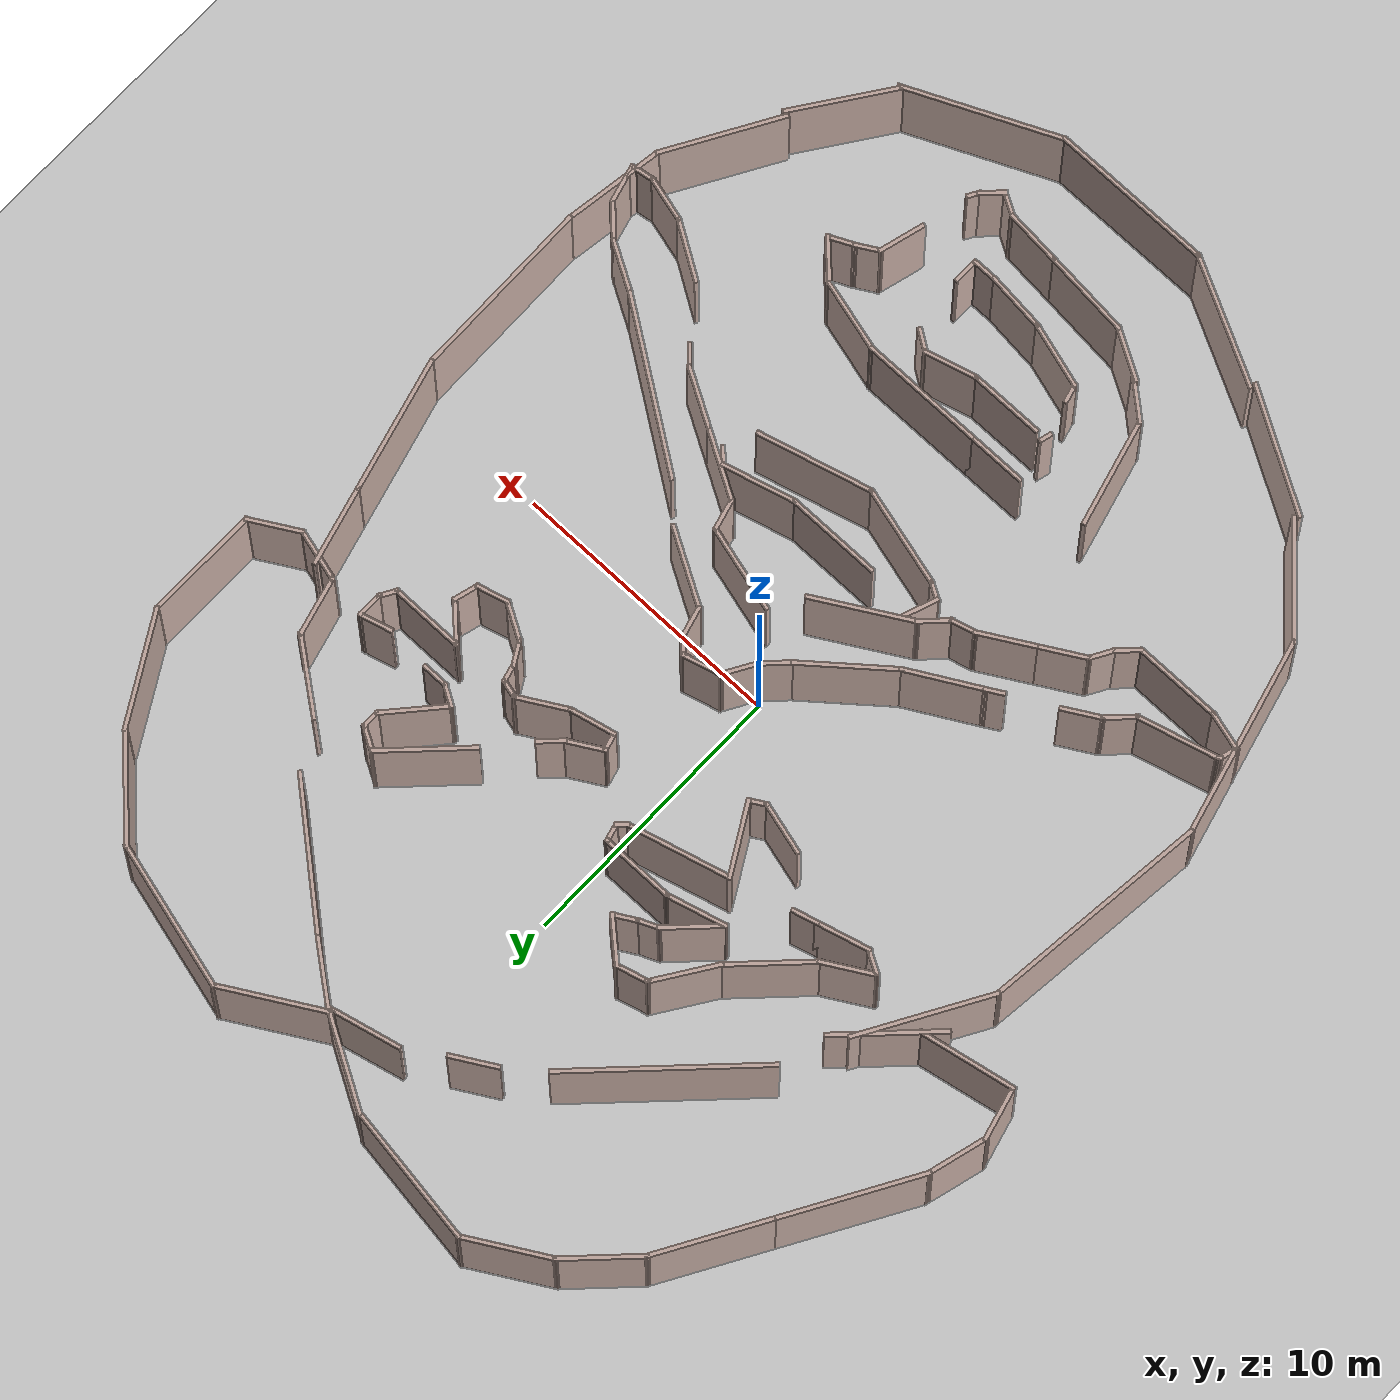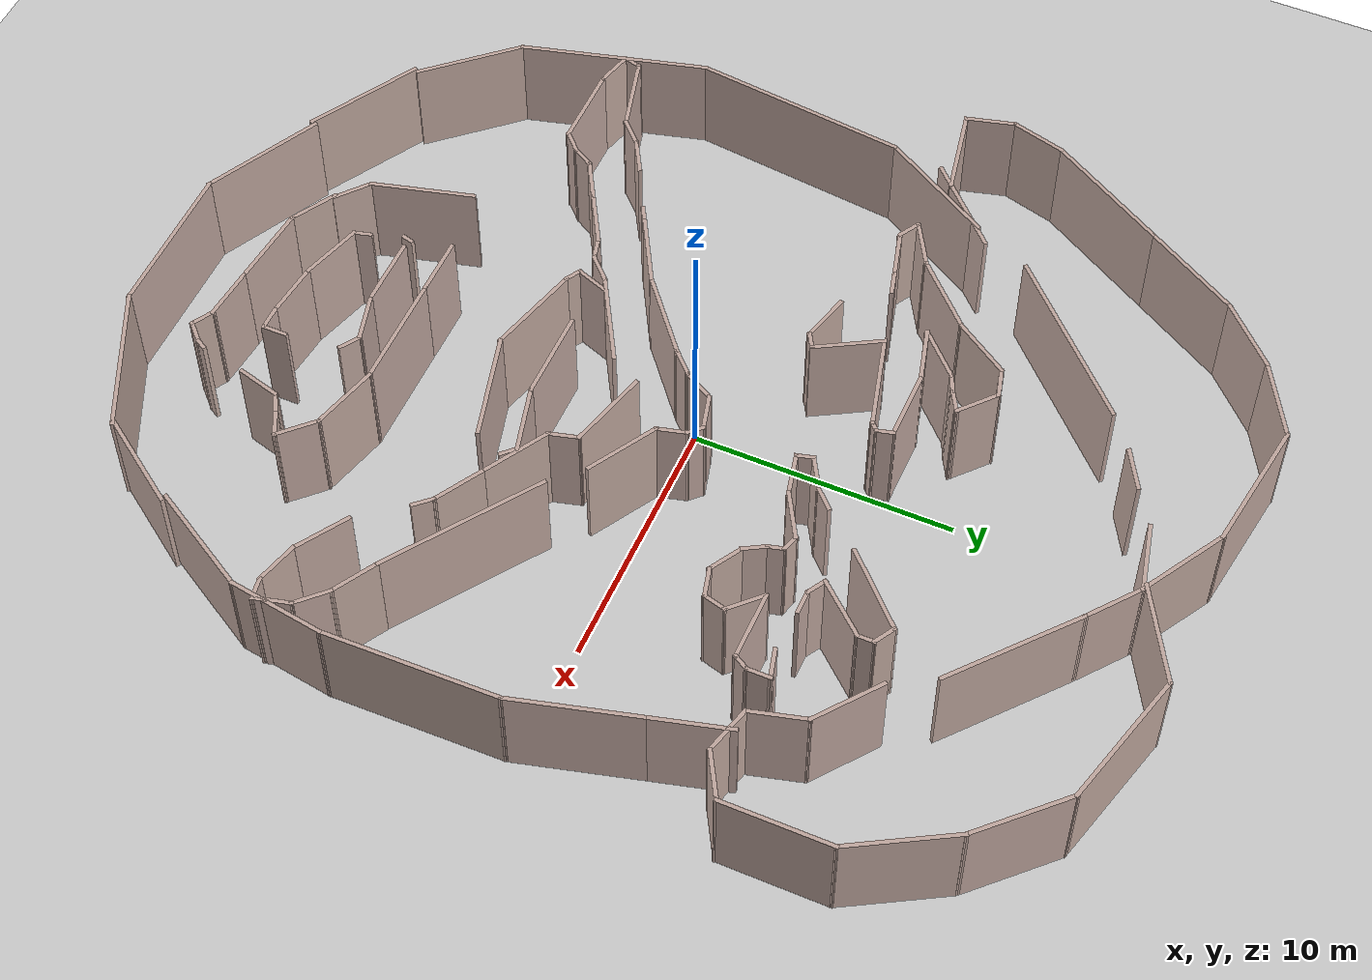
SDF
<sdf version="1.7">
 <world name="default">
  <plugin name="ros_interface_plugin" filename="librotors_gazebo_ros_interface_plugin.so"/>
  <light name="sun" type="directional">
   <pose>0 0 10 0 -0 0</pose>
   <diffuse>0.8 0.8 0.8 1</diffuse>
   <specular>0.2 0.2 0.2 1</specular>
   <attenuation>
    <range>1000</range>
    <constant>0.9</constant>
    <linear>0.01</linear>
    <quadratic>0.001</quadratic>
   </attenuation>
   <direction>-0.5 0.1 -0.9</direction>
   <spot><inner_angle>0</inner_angle><outer_angle>0</outer_angle><falloff>0</falloff></spot>
  </light>
  <model name="ground_plane">
   <static>1</static>
   <link name="link">
    <collision name="collision">
     <geometry><plane><normal>0 0 1</normal><size>100 100</size></plane></geometry>
     <surface><friction><ode><mu>100</mu><mu2>50</mu2></ode></friction></surface>
    </collision>
    <visual name="visual">
     <cast_shadows>0</cast_shadows>
     <geometry><plane><normal>0 0 1</normal><size>100 100</size></plane></geometry>
     <material>
      <script><uri>file://media/materials/scripts/gazebo.material</uri><name>Gazebo/Grey</name></script>
     </material>
    </visual>
   </link>
  </model>
  <gravity>0 0 -9.8</gravity>
  <magnetic_field>6e-06 2.3e-05 -4.2e-05</magnetic_field>
  <atmosphere type="adiabatic"/>
  <physics type="ode">
   <max_step_size>0.001</max_step_size>
   <real_time_factor>1</real_time_factor>
   <real_time_update_rate>1000</real_time_update_rate>
  </physics>
  <scene><ambient>0.4 0.4 0.4 1</ambient><background>0.7 0.7 0.7 1</background><shadows>1</shadows></scene>
  <spherical_coordinates>
   <surface_model>EARTH_WGS84</surface_model>
   <latitude_deg>0</latitude_deg>
   <longitude_deg>0</longitude_deg>
   <elevation>0</elevation>
   <heading_deg>0</heading_deg>
  </spherical_coordinates>
  <model name="Untitled">
   <pose>-0.071284 -0.040454 0 0 -0 0</pose>
   <link name="Wall_100">
    <collision name="Wall_100_Collision">
     <geometry><box><size>8.26296 0.15 4.0</size></box></geometry>
     <pose>0 0 2.0 0 -0 0</pose>
    </collision>
    <visual name="Wall_100_Visual">
     <pose>0 0 2.0 0 -0 0</pose>
     <geometry><box><size>8.26296 0.15 4.0</size></box></geometry>
     <material>
      <script><uri>file://media/materials/scripts/gazebo.material</uri><name>Gazebo/Grey</name></script>
      <ambient>0.760784 0.662745 0.627451 1</ambient>
     </material>
     <meta><layer>0</layer></meta>
    </visual>
    <pose>-13.0327 -1.43511 0 0 -0 -1.67725</pose>
   </link>
   <link name="Wall_102">
    <collision name="Wall_102_Collision">
     <geometry><box><size>3.76572 0.15 4.0</size></box></geometry>
     <pose>0 0 2.0 0 -0 0</pose>
    </collision>
    <visual name="Wall_102_Visual">
     <pose>0 0 2.0 0 -0 0</pose>
     <geometry><box><size>3.76572 0.15 4.0</size></box></geometry>
     <material>
      <script><uri>file://media/materials/scripts/gazebo.material</uri><name>Gazebo/Grey</name></script>
      <ambient>0.760784 0.662745 0.627451 1</ambient>
     </material>
     <meta><layer>0</layer></meta>
    </visual>
    <pose>14.7329 -8.7065 0 0 -0 1.42378</pose>
   </link>
   <link name="Wall_103">
    <collision name="Wall_103_Collision">
     <geometry><box><size>6.73423 0.15 4.0</size></box></geometry>
     <pose>0 0 2.0 0 -0 0</pose>
    </collision>
    <visual name="Wall_103_Visual">
     <pose>0 0 2.0 0 -0 0</pose>
     <geometry><box><size>6.73423 0.15 4.0</size></box></geometry>
     <material>
      <script><uri>file://media/materials/scripts/gazebo.material</uri><name>Gazebo/Grey</name></script>
      <ambient>0.760784 0.662745 0.627451 1</ambient>
     </material>
     <meta><layer>0</layer></meta>
    </visual>
    <pose>14.933 -3.62666 0 0 -0 1.59045</pose>
   </link>
   <link name="Wall_104">
    <collision name="Wall_104_Collision">
     <geometry><box><size>5 0.15 4.0</size></box></geometry>
     <pose>0 0 2.0 0 -0 0</pose>
    </collision>
    <visual name="Wall_104_Visual">
     <pose>0 0 2.0 0 -0 0</pose>
     <geometry><box><size>5 0.15 4.0</size></box></geometry>
     <material>
      <script><uri>file://media/materials/scripts/gazebo.material</uri><name>Gazebo/Grey</name></script>
      <ambient>0.760784 0.662745 0.627451 1</ambient>
     </material>
     <meta><layer>0</layer></meta>
    </visual>
    <pose>14.2407 2.00719 0 0 -0 1.8326</pose>
   </link>
   <link name="Wall_105">
    <collision name="Wall_105_Collision">
     <geometry><box><size>3 0.15 4.0</size></box></geometry>
     <pose>0 0 2.0 0 -0 0</pose>
    </collision>
    <visual name="Wall_105_Visual">
     <pose>0 0 2.0 0 -0 0</pose>
     <geometry><box><size>3 0.15 4.0</size></box></geometry>
     <material>
      <script><uri>file://media/materials/scripts/gazebo.material</uri><name>Gazebo/Grey</name></script>
      <ambient>0.760784 0.662745 0.627451 1</ambient>
     </material>
     <meta><layer>0</layer></meta>
    </visual>
    <pose>13.2443 5.726 0 0 -0 1.8326</pose>
   </link>
   <link name="Wall_107">
    <collision name="Wall_107_Collision">
     <geometry><box><size>2.52892 0.15 4.0</size></box></geometry>
     <pose>0 0 2.0 0 -0 0</pose>
    </collision>
    <visual name="Wall_107_Visual">
     <pose>0 0 2.0 0 -0 0</pose>
     <geometry><box><size>2.52892 0.15 4.0</size></box></geometry>
     <material>
      <script><uri>file://media/materials/scripts/gazebo.material</uri><name>Gazebo/Grey</name></script>
      <ambient>0.760784 0.662745 0.627451 1</ambient>
     </material>
     <meta><layer>0</layer></meta>
    </visual>
    <pose>-4.96725 8.86569 0 0 -0 -2.15329</pose>
   </link>
   <link name="Wall_110">
    <collision name="Wall_110_Collision">
     <geometry><box><size>3.25 0.15 4.0</size></box></geometry>
     <pose>0 0 2.0 0 -0 0</pose>
    </collision>
    <visual name="Wall_110_Visual">
     <pose>0 0 2.0 0 -0 0</pose>
     <geometry><box><size>3.25 0.15 4.0</size></box></geometry>
     <material>
      <script><uri>file://media/materials/scripts/gazebo.material</uri><name>Gazebo/Grey</name></script>
      <ambient>0.760784 0.662745 0.627451 1</ambient>
     </material>
     <meta><layer>0</layer></meta>
    </visual>
    <pose>-6.7176 6.77637 0 0 -0 -2.35619</pose>
   </link>
   <link name="Wall_111">
    <collision name="Wall_111_Collision">
     <geometry><box><size>2 0.15 4.0</size></box></geometry>
     <pose>0 0 2.0 0 -0 0</pose>
    </collision>
    <visual name="Wall_111_Visual">
     <pose>0 0 2.0 0 -0 0</pose>
     <geometry><box><size>2 0.15 4.0</size></box></geometry>
     <material>
      <script><uri>file://media/materials/scripts/gazebo.material</uri><name>Gazebo/Grey</name></script>
      <ambient>0.760784 0.662745 0.627451 1</ambient>
     </material>
     <meta><layer>0</layer></meta>
    </visual>
    <pose>-8.61469 5.21785 0 0 -0 -2.61799</pose>
   </link>
   <link name="Wall_112">
    <collision name="Wall_112_Collision">
     <geometry><box><size>1 0.15 4.0</size></box></geometry>
     <pose>0 0 2.0 0 -0 0</pose>
    </collision>
    <visual name="Wall_112_Visual">
     <pose>0 0 2.0 0 -0 0</pose>
     <geometry><box><size>1 0.15 4.0</size></box></geometry>
     <material>
      <script><uri>file://media/materials/scripts/gazebo.material</uri><name>Gazebo/Grey</name></script>
      <ambient>0.760784 0.662745 0.627451 1</ambient>
     </material>
     <meta><layer>0</layer></meta>
    </visual>
    <pose>-9.0477 4.54285 0 0 -0 -0.523599</pose>
   </link>
   <link name="Wall_113">
    <collision name="Wall_113_Collision">
     <geometry><box><size>2 0.15 4.0</size></box></geometry>
     <pose>0 0 2.0 0 -0 0</pose>
    </collision>
    <visual name="Wall_113_Visual">
     <pose>0 0 2.0 0 -0 0</pose>
     <geometry><box><size>2 0.15 4.0</size></box></geometry>
     <material>
      <script><uri>file://media/materials/scripts/gazebo.material</uri><name>Gazebo/Grey</name></script>
      <ambient>0.760784 0.662745 0.627451 1</ambient>
     </material>
     <meta><layer>0</layer></meta>
    </visual>
    <pose>-7.78616 4.56976 0 0 -0 0.261799</pose>
   </link>
   <link name="Wall_114">
    <collision name="Wall_114_Collision">
     <geometry><box><size>1 0.15 4.0</size></box></geometry>
     <pose>0 0 2.0 0 -0 0</pose>
    </collision>
    <visual name="Wall_114_Visual">
     <pose>0 0 2.0 0 -0 0</pose>
     <geometry><box><size>1 0.15 4.0</size></box></geometry>
     <material>
      <script><uri>file://media/materials/scripts/gazebo.material</uri><name>Gazebo/Grey</name></script>
      <ambient>0.760784 0.662745 0.627451 1</ambient>
     </material>
     <meta><layer>0</layer></meta>
    </visual>
    <pose>-6.48216 4.91916 0 0 -0 0.261799</pose>
   </link>
   <link name="Wall_116">
    <collision name="Wall_116_Collision">
     <geometry><box><size>3.75 0.15 4.0</size></box></geometry>
     <pose>0 0 2.0 0 -0 0</pose>
    </collision>
    <visual name="Wall_116_Visual">
     <pose>0 0 2.0 0 -0 0</pose>
     <geometry><box><size>3.75 0.15 4.0</size></box></geometry>
     <material>
      <script><uri>file://media/materials/scripts/gazebo.material</uri><name>Gazebo/Grey</name></script>
      <ambient>0.760784 0.662745 0.627451 1</ambient>
     </material>
     <meta><layer>0</layer></meta>
    </visual>
    <pose>-2.06305 6.10326 0 0 -0 0.261799</pose>
   </link>
   <link name="Wall_117">
    <collision name="Wall_117_Collision">
     <geometry><box><size>0.5 0.15 4.0</size></box></geometry>
     <pose>0 0 2.0 0 -0 0</pose>
    </collision>
    <visual name="Wall_117_Visual">
     <pose>0 0 2.0 0 -0 0</pose>
     <geometry><box><size>0.5 0.15 4.0</size></box></geometry>
     <material>
      <script><uri>file://media/materials/scripts/gazebo.material</uri><name>Gazebo/Grey</name></script>
      <ambient>0.760784 0.662745 0.627451 1</ambient>
     </material>
     <meta><layer>0</layer></meta>
    </visual>
    <pose>-0.200637 6.69288 0 0 -0 0.785398</pose>
   </link>
   <link name="Wall_118">
    <collision name="Wall_118_Collision">
     <geometry><box><size>0.75 0.15 4.0</size></box></geometry>
     <pose>0 0 2.0 0 -0 0</pose>
    </collision>
    <visual name="Wall_118_Visual">
     <pose>0 0 2.0 0 -0 0</pose>
     <geometry><box><size>0.75 0.15 4.0</size></box></geometry>
     <material>
      <script><uri>file://media/materials/scripts/gazebo.material</uri><name>Gazebo/Grey</name></script>
      <ambient>0.760784 0.662745 0.627451 1</ambient>
     </material>
     <meta><layer>0</layer></meta>
    </visual>
    <pose>-0.154539 7.1064 0 0 -0 1.8326</pose>
   </link>
   <link name="Wall_119">
    <collision name="Wall_119_Collision">
     <geometry><box><size>2.75 0.15 4.0</size></box></geometry>
     <pose>0 0 2.0 0 -0 0</pose>
    </collision>
    <visual name="Wall_119_Visual">
     <pose>0 0 2.0 0 -0 0</pose>
     <geometry><box><size>2.75 0.15 4.0</size></box></geometry>
     <material>
      <script><uri>file://media/materials/scripts/gazebo.material</uri><name>Gazebo/Grey</name></script>
      <ambient>0.760784 0.662745 0.627451 1</ambient>
     </material>
     <meta><layer>0</layer></meta>
    </visual>
    <pose>-1.53218 7.39618 0 0 -0 3.14159</pose>
   </link>
   <link name="Wall_120">
    <collision name="Wall_120_Collision">
     <geometry><box><size>2.25 0.15 4.0</size></box></geometry>
     <pose>0 0 2.0 0 -0 0</pose>
    </collision>
    <visual name="Wall_120_Visual">
     <pose>0 0 2.0 0 -0 0</pose>
     <geometry><box><size>2.25 0.15 4.0</size></box></geometry>
     <material>
      <script><uri>file://media/materials/scripts/gazebo.material</uri><name>Gazebo/Grey</name></script>
      <ambient>0.760784 0.662745 0.627451 1</ambient>
     </material>
     <meta><layer>0</layer></meta>
    </visual>
    <pose>-3.84641 7.12442 0 0 -0 -2.87979</pose>
   </link>
   <link name="Wall_121">
    <collision name="Wall_121_Collision">
     <geometry><box><size>2.25 0.15 4.0</size></box></geometry>
     <pose>0 0 2.0 0 -0 0</pose>
    </collision>
    <visual name="Wall_121_Visual">
     <pose>0 0 2.0 0 -0 0</pose>
     <geometry><box><size>2.25 0.15 4.0</size></box></geometry>
     <material>
      <script><uri>file://media/materials/scripts/gazebo.material</uri><name>Gazebo/Grey</name></script>
      <ambient>0.760784 0.662745 0.627451 1</ambient>
     </material>
     <meta><layer>0</layer></meta>
    </visual>
    <pose>-4.11817 7.59512 0 0 -0 0.785398</pose>
   </link>
   <link name="Wall_122">
    <collision name="Wall_122_Collision">
     <geometry><box><size>0.842842 0.15 4.0</size></box></geometry>
     <pose>0 0 2.0 0 -0 0</pose>
    </collision>
    <visual name="Wall_122_Visual">
     <pose>0 0 2.0 0 -0 0</pose>
     <geometry><box><size>0.842842 0.15 4.0</size></box></geometry>
     <material>
      <script><uri>file://media/materials/scripts/gazebo.material</uri><name>Gazebo/Grey</name></script>
      <ambient>0.760784 0.662745 0.627451 1</ambient>
     </material>
     <meta><layer>0</layer></meta>
    </visual>
    <pose>-3.05895 8.47785 0 0 -0 0.416862</pose>
   </link>
   <link name="Wall_123">
    <collision name="Wall_123_Collision">
     <geometry><box><size>1 0.15 4.0</size></box></geometry>
     <pose>0 0 2.0 0 -0 0</pose>
    </collision>
    <visual name="Wall_123_Visual">
     <pose>0 0 2.0 0 -0 0</pose>
     <geometry><box><size>1 0.15 4.0</size></box></geometry>
     <material>
      <script><uri>file://media/materials/scripts/gazebo.material</uri><name>Gazebo/Grey</name></script>
      <ambient>0.760784 0.662745 0.627451 1</ambient>
     </material>
     <meta><layer>0</layer></meta>
    </visual>
    <pose>-2.37413 8.83061 0 0 -0 0.523599</pose>
   </link>
   <link name="Wall_124">
    <collision name="Wall_124_Collision">
     <geometry><box><size>1.81122 0.15 4.0</size></box></geometry>
     <pose>0 0 2.0 0 -0 0</pose>
    </collision>
    <visual name="Wall_124_Visual">
     <pose>0 0 2.0 0 -0 0</pose>
     <geometry><box><size>1.81122 0.15 4.0</size></box></geometry>
     <material>
      <script><uri>file://media/materials/scripts/gazebo.material</uri><name>Gazebo/Grey</name></script>
      <ambient>0.760784 0.662745 0.627451 1</ambient>
     </material>
     <meta><layer>0</layer></meta>
    </visual>
    <pose>-2.62824 9.59341 0 0 -0 2.41741</pose>
   </link>
   <link name="Wall_125">
    <collision name="Wall_125_Collision">
     <geometry><box><size>1.25 0.15 4.0</size></box></geometry>
     <pose>0 0 2.0 0 -0 0</pose>
    </collision>
    <visual name="Wall_125_Visual">
     <pose>0 0 2.0 0 -0 0</pose>
     <geometry><box><size>1.25 0.15 4.0</size></box></geometry>
     <material>
      <script><uri>file://media/materials/scripts/gazebo.material</uri><name>Gazebo/Grey</name></script>
      <ambient>0.760784 0.662745 0.627451 1</ambient>
     </material>
     <meta><layer>0</layer></meta>
    </visual>
    <pose>-3.78166 10.0014 0 0 -0 -2.87979</pose>
   </link>
   <link name="Wall_127">
    <collision name="Wall_127_Collision">
     <geometry><box><size>1 0.15 4.0</size></box></geometry>
     <pose>0 0 2.0 0 -0 0</pose>
    </collision>
    <visual name="Wall_127_Visual">
     <pose>0 0 2.0 0 -0 0</pose>
     <geometry><box><size>1 0.15 4.0</size></box></geometry>
     <material>
      <script><uri>file://media/materials/scripts/gazebo.material</uri><name>Gazebo/Grey</name></script>
      <ambient>0.760784 0.662745 0.627451 1</ambient>
     </material>
     <meta><layer>0</layer></meta>
    </visual>
    <pose>7.60765 10.1462 0 0 -0 -0.523599</pose>
   </link>
   <link name="Wall_128">
    <collision name="Wall_128_Collision">
     <geometry><box><size>0.75 0.15 4.0</size></box></geometry>
     <pose>0 0 2.0 0 -0 0</pose>
    </collision>
    <visual name="Wall_128_Visual">
     <pose>0 0 2.0 0 -0 0</pose>
     <geometry><box><size>0.75 0.15 4.0</size></box></geometry>
     <material>
      <script><uri>file://media/materials/scripts/gazebo.material</uri><name>Gazebo/Grey</name></script>
      <ambient>0.760784 0.662745 0.627451 1</ambient>
     </material>
     <meta><layer>0</layer></meta>
    </visual>
    <pose>7.97571 9.6337 0 0 -0 -1.5708</pose>
   </link>
   <link name="Wall_129">
    <collision name="Wall_129_Collision">
     <geometry><box><size>2.50487 0.15 4.0</size></box></geometry>
     <pose>0 0 2.0 0 -0 0</pose>
    </collision>
    <visual name="Wall_129_Visual">
     <pose>0 0 2.0 0 -0 0</pose>
     <geometry><box><size>2.50487 0.15 4.0</size></box></geometry>
     <material>
      <script><uri>file://media/materials/scripts/gazebo.material</uri><name>Gazebo/Grey</name></script>
      <ambient>0.760784 0.662745 0.627451 1</ambient>
     </material>
     <meta><layer>0</layer></meta>
    </visual>
    <pose>7.19836 8.44935 0 0 -0 -2.29189</pose>
   </link>
   <link name="Wall_132">
    <collision name="Wall_132_Collision">
     <geometry><box><size>1.25 0.15 4.0</size></box></geometry>
     <pose>0 0 2.0 0 -0 0</pose>
    </collision>
    <visual name="Wall_132_Visual">
     <pose>0 0 2.0 0 -0 0</pose>
     <geometry><box><size>1.25 0.15 4.0</size></box></geometry>
     <material>
      <script><uri>file://media/materials/scripts/gazebo.material</uri><name>Gazebo/Grey</name></script>
      <ambient>0.760784 0.662745 0.627451 1</ambient>
     </material>
     <meta><layer>0</layer></meta>
    </visual>
    <pose>10.0942 7.21331 0 0 -0 0.261799</pose>
   </link>
   <link name="Wall_133">
    <collision name="Wall_133_Collision">
     <geometry><box><size>1 0.15 4.0</size></box></geometry>
     <pose>0 0 2.0 0 -0 0</pose>
    </collision>
    <visual name="Wall_133_Visual">
     <pose>0 0 2.0 0 -0 0</pose>
     <geometry><box><size>1 0.15 4.0</size></box></geometry>
     <material>
      <script><uri>file://media/materials/scripts/gazebo.material</uri><name>Gazebo/Grey</name></script>
      <ambient>0.760784 0.662745 0.627451 1</ambient>
     </material>
     <meta><layer>0</layer></meta>
    </visual>
    <pose>10.6255 6.93066 0 0 -0 -1.5708</pose>
   </link>
   <link name="Wall_134">
    <collision name="Wall_134_Collision">
     <geometry><box><size>0.75 0.15 4.0</size></box></geometry>
     <pose>0 0 2.0 0 -0 0</pose>
    </collision>
    <visual name="Wall_134_Visual">
     <pose>0 0 2.0 0 -0 0</pose>
     <geometry><box><size>0.75 0.15 4.0</size></box></geometry>
     <material>
      <script><uri>file://media/materials/scripts/gazebo.material</uri><name>Gazebo/Grey</name></script>
      <ambient>0.760784 0.662745 0.627451 1</ambient>
     </material>
     <meta><layer>0</layer></meta>
    </visual>
    <pose>10.4755 6.24585 0 0 -0 -2.0944</pose>
   </link>
   <link name="Wall_135">
    <collision name="Wall_135_Collision">
     <geometry><box><size>2.75 0.15 4.0</size></box></geometry>
     <pose>0 0 2.0 0 -0 0</pose>
    </collision>
    <visual name="Wall_135_Visual">
     <pose>0 0 2.0 0 -0 0</pose>
     <geometry><box><size>2.75 0.15 4.0</size></box></geometry>
     <material>
      <script><uri>file://media/materials/scripts/gazebo.material</uri><name>Gazebo/Grey</name></script>
      <ambient>0.760784 0.662745 0.627451 1</ambient>
     </material>
     <meta><layer>0</layer></meta>
    </visual>
    <pose>9.02549 5.98605 0 0 -0 3.14159</pose>
   </link>
   <link name="Wall_136">
    <collision name="Wall_136_Collision">
     <geometry><box><size>1.64817 0.15 4.0</size></box></geometry>
     <pose>0 0 2.0 0 -0 0</pose>
    </collision>
    <visual name="Wall_136_Visual">
     <pose>0 0 2.0 0 -0 0</pose>
     <geometry><box><size>1.64817 0.15 4.0</size></box></geometry>
     <material>
      <script><uri>file://media/materials/scripts/gazebo.material</uri><name>Gazebo/Grey</name></script>
      <ambient>0.760784 0.662745 0.627451 1</ambient>
     </material>
     <meta><layer>0</layer></meta>
    </visual>
    <pose>8.25981 5.46105 0 0 -0 -0.776594</pose>
   </link>
   <link name="Wall_137">
    <collision name="Wall_137_Collision">
     <geometry><box><size>1 0.15 4.0</size></box></geometry>
     <pose>0 0 2.0 0 -0 0</pose>
    </collision>
    <visual name="Wall_137_Visual">
     <pose>0 0 2.0 0 -0 0</pose>
     <geometry><box><size>1 0.15 4.0</size></box></geometry>
     <material>
      <script><uri>file://media/materials/scripts/gazebo.material</uri><name>Gazebo/Grey</name></script>
      <ambient>0.760784 0.662745 0.627451 1</ambient>
     </material>
     <meta><layer>0</layer></meta>
    </visual>
    <pose>8.68414 4.52553 0 0 -0 -1.8326</pose>
   </link>
   <link name="Wall_138">
    <collision name="Wall_138_Collision">
     <geometry><box><size>1.25 0.15 4.0</size></box></geometry>
     <pose>0 0 2.0 0 -0 0</pose>
    </collision>
    <visual name="Wall_138_Visual">
     <pose>0 0 2.0 0 -0 0</pose>
     <geometry><box><size>1.25 0.15 4.0</size></box></geometry>
     <material>
      <script><uri>file://media/materials/scripts/gazebo.material</uri><name>Gazebo/Grey</name></script>
      <ambient>0.760784 0.662745 0.627451 1</ambient>
     </material>
     <meta><layer>0</layer></meta>
    </visual>
    <pose>8.04288 3.97266 0 0 -0 -2.87979</pose>
   </link>
   <link name="Wall_139">
    <collision name="Wall_139_Collision">
     <geometry><box><size>1.5 0.15 4.0</size></box></geometry>
     <pose>0 0 2.0 0 -0 0</pose>
    </collision>
    <visual name="Wall_139_Visual">
     <pose>0 0 2.0 0 -0 0</pose>
     <geometry><box><size>1.5 0.15 4.0</size></box></geometry>
     <material>
      <script><uri>file://media/materials/scripts/gazebo.material</uri><name>Gazebo/Grey</name></script>
      <ambient>0.760784 0.662745 0.627451 1</ambient>
     </material>
     <meta><layer>0</layer></meta>
    </visual>
    <pose>6.92706 4.16781 0 0 -0 2.61799</pose>
   </link>
   <link name="Wall_140">
    <collision name="Wall_140_Collision">
     <geometry><box><size>1 0.15 4.0</size></box></geometry>
     <pose>0 0 2.0 0 -0 0</pose>
    </collision>
    <visual name="Wall_140_Visual">
     <pose>0 0 2.0 0 -0 0</pose>
     <geometry><box><size>1 0.15 4.0</size></box></geometry>
     <material>
      <script><uri>file://media/materials/scripts/gazebo.material</uri><name>Gazebo/Grey</name></script>
      <ambient>0.760784 0.662745 0.627451 1</ambient>
     </material>
     <meta><layer>0</layer></meta>
    </visual>
    <pose>6.12999 4.87337 0 0 -0 2.0944</pose>
   </link>
   <link name="Wall_141">
    <collision name="Wall_141_Collision">
     <geometry><box><size>0.75 0.15 4.0</size></box></geometry>
     <pose>0 0 2.0 0 -0 0</pose>
    </collision>
    <visual name="Wall_141_Visual">
     <pose>0 0 2.0 0 -0 0</pose>
     <geometry><box><size>0.75 0.15 4.0</size></box></geometry>
     <material>
      <script><uri>file://media/materials/scripts/gazebo.material</uri><name>Gazebo/Grey</name></script>
      <ambient>0.760784 0.662745 0.627451 1</ambient>
     </material>
     <meta><layer>0</layer></meta>
    </visual>
    <pose>5.83985 5.53121 0 0 -0 1.8326</pose>
   </link>
   <link name="Wall_142">
    <collision name="Wall_142_Collision">
     <geometry><box><size>0.75 0.15 4.0</size></box></geometry>
     <pose>0 0 2.0 0 -0 0</pose>
    </collision>
    <visual name="Wall_142_Visual">
     <pose>0 0 2.0 0 -0 0</pose>
     <geometry><box><size>0.75 0.15 4.0</size></box></geometry>
     <material>
      <script><uri>file://media/materials/scripts/gazebo.material</uri><name>Gazebo/Grey</name></script>
      <ambient>0.760784 0.662745 0.627451 1</ambient>
     </material>
     <meta><layer>0</layer></meta>
    </visual>
    <pose>5.47242 5.89863 0 0 -0 2.87979</pose>
   </link>
   <link name="Wall_143">
    <collision name="Wall_143_Collision">
     <geometry><box><size>2 0.15 4.0</size></box></geometry>
     <pose>0 0 2.0 0 -0 0</pose>
    </collision>
    <visual name="Wall_143_Visual">
     <pose>0 0 2.0 0 -0 0</pose>
     <geometry><box><size>2 0.15 4.0</size></box></geometry>
     <material>
      <script><uri>file://media/materials/scripts/gazebo.material</uri><name>Gazebo/Grey</name></script>
      <ambient>0.760784 0.662745 0.627451 1</ambient>
     </material>
     <meta><layer>0</layer></meta>
    </visual>
    <pose>4.38157 5.51378 0 0 -0 -2.61799</pose>
   </link>
   <link name="Wall_144">
    <collision name="Wall_144_Collision">
     <geometry><box><size>1.75232 0.15 4.0</size></box></geometry>
     <pose>0 0 2.0 0 -0 0</pose>
    </collision>
    <visual name="Wall_144_Visual">
     <pose>0 0 2.0 0 -0 0</pose>
     <geometry><box><size>1.75232 0.15 4.0</size></box></geometry>
     <material>
      <script><uri>file://media/materials/scripts/gazebo.material</uri><name>Gazebo/Grey</name></script>
      <ambient>0.760784 0.662745 0.627451 1</ambient>
     </material>
     <meta><layer>0</layer></meta>
    </visual>
    <pose>2.80009 4.87013 0 0 -0 -2.91351</pose>
   </link>
   <link name="Wall_145">
    <collision name="Wall_145_Collision">
     <geometry><box><size>0.75 0.15 4.0</size></box></geometry>
     <pose>0 0 2.0 0 -0 0</pose>
    </collision>
    <visual name="Wall_145_Visual">
     <pose>0 0 2.0 0 -0 0</pose>
     <geometry><box><size>0.75 0.15 4.0</size></box></geometry>
     <material>
      <script><uri>file://media/materials/scripts/gazebo.material</uri><name>Gazebo/Grey</name></script>
      <ambient>0.760784 0.662745 0.627451 1</ambient>
     </material>
     <meta><layer>0</layer></meta>
    </visual>
    <pose>1.94203 4.97876 0 0 -0 1.8326</pose>
   </link>
   <link name="Wall_147">
    <collision name="Wall_147_Collision">
     <geometry><box><size>3.5 0.15 4.0</size></box></geometry>
     <pose>0 0 2.0 0 -0 0</pose>
    </collision>
    <visual name="Wall_147_Visual">
     <pose>0 0 2.0 0 -0 0</pose>
     <geometry><box><size>3.5 0.15 4.0</size></box></geometry>
     <material>
      <script><uri>file://media/materials/scripts/gazebo.material</uri><name>Gazebo/Grey</name></script>
      <ambient>0.760784 0.662745 0.627451 1</ambient>
     </material>
     <meta><layer>0</layer></meta>
    </visual>
    <pose>6.05518 9.1743 0 0 -0 0.785398</pose>
   </link>
   <link name="Wall_158">
    <collision name="Wall_158_Collision">
     <geometry><box><size>2 0.15 4.0</size></box></geometry>
     <pose>0 0 2.0 0 -0 0</pose>
    </collision>
    <visual name="Wall_158_Visual">
     <pose>0 0 2.0 0 -0 0</pose>
     <geometry><box><size>2 0.15 4.0</size></box></geometry>
     <material>
      <script><uri>file://media/materials/scripts/gazebo.material</uri><name>Gazebo/Grey</name></script>
      <ambient>0.760784 0.662745 0.627451 1</ambient>
     </material>
     <meta><layer>0</layer></meta>
    </visual>
    <pose>-3.98469 3.31005 0 0 -0 -0.261799</pose>
   </link>
   <link name="Wall_159">
    <collision name="Wall_159_Collision">
     <geometry><box><size>0.75 0.15 4.0</size></box></geometry>
     <pose>0 0 2.0 0 -0 0</pose>
    </collision>
    <visual name="Wall_159_Visual">
     <pose>0 0 2.0 0 -0 0</pose>
     <geometry><box><size>0.75 0.15 4.0</size></box></geometry>
     <material>
      <script><uri>file://media/materials/scripts/gazebo.material</uri><name>Gazebo/Grey</name></script>
      <ambient>0.760784 0.662745 0.627451 1</ambient>
     </material>
     <meta><layer>0</layer></meta>
    </visual>
    <pose>-2.83141 3.22065 0 0 -0 0.523599</pose>
   </link>
   <link name="Wall_160">
    <collision name="Wall_160_Collision">
     <geometry><box><size>2.75 0.15 4.0</size></box></geometry>
     <pose>0 0 2.0 0 -0 0</pose>
    </collision>
    <visual name="Wall_160_Visual">
     <pose>0 0 2.0 0 -0 0</pose>
     <geometry><box><size>2.75 0.15 4.0</size></box></geometry>
     <material>
      <script><uri>file://media/materials/scripts/gazebo.material</uri><name>Gazebo/Grey</name></script>
      <ambient>0.760784 0.662745 0.627451 1</ambient>
     </material>
     <meta><layer>0</layer></meta>
    </visual>
    <pose>-3.2216 4.49648 0 0 -0 2.0944</pose>
   </link>
   <link name="Wall_166">
    <collision name="Wall_166_Collision">
     <geometry><box><size>1.25 0.15 4.0</size></box></geometry>
     <pose>0 0 2.0 0 -0 0</pose>
    </collision>
    <visual name="Wall_166_Visual">
     <pose>0 0 2.0 0 -0 0</pose>
     <geometry><box><size>1.25 0.15 4.0</size></box></geometry>
     <material>
      <script><uri>file://media/materials/scripts/gazebo.material</uri><name>Gazebo/Grey</name></script>
      <ambient>0.760784 0.662745 0.627451 1</ambient>
     </material>
     <meta><layer>0</layer></meta>
    </visual>
    <pose>-0.087721 -0.522776 0 0 -0 -2.35619</pose>
   </link>
   <link name="Wall_167">
    <collision name="Wall_167_Collision">
     <geometry><box><size>3.59762 0.15 4.0</size></box></geometry>
     <pose>0 0 2.0 0 -0 0</pose>
    </collision>
    <visual name="Wall_167_Visual">
     <pose>0 0 2.0 0 -0 0</pose>
     <geometry><box><size>3.59762 0.15 4.0</size></box></geometry>
     <material>
      <script><uri>file://media/materials/scripts/gazebo.material</uri><name>Gazebo/Grey</name></script>
      <ambient>0.760784 0.662745 0.627451 1</ambient>
     </material>
     <meta><layer>0</layer></meta>
    </visual>
    <pose>-1.80589 -2.00922 0 0 -0 -2.45139</pose>
   </link>
   <link name="Wall_168">
    <collision name="Wall_168_Collision">
     <geometry><box><size>2.9108 0.15 4.0</size></box></geometry>
     <pose>0 0 2.0 0 -0 0</pose>
    </collision>
    <visual name="Wall_168_Visual">
     <pose>0 0 2.0 0 -0 0</pose>
     <geometry><box><size>2.9108 0.15 4.0</size></box></geometry>
     <material>
      <script><uri>file://media/materials/scripts/gazebo.material</uri><name>Gazebo/Grey</name></script>
      <ambient>0.760784 0.662745 0.627451 1</ambient>
     </material>
     <meta><layer>0</layer></meta>
    </visual>
    <pose>-4.33918 -3.78189 0 0 -0 -2.63056</pose>
   </link>
   <link name="Wall_170">
    <collision name="Wall_170_Collision">
     <geometry><box><size>0.75 0.15 4.0</size></box></geometry>
     <pose>0 0 2.0 0 -0 0</pose>
    </collision>
    <visual name="Wall_170_Visual">
     <pose>0 0 2.0 0 -0 0</pose>
     <geometry><box><size>0.75 0.15 4.0</size></box></geometry>
     <material>
      <script><uri>file://media/materials/scripts/gazebo.material</uri><name>Gazebo/Grey</name></script>
      <ambient>0.760784 0.662745 0.627451 1</ambient>
     </material>
     <meta><layer>0</layer></meta>
    </visual>
    <pose>-5.80303 -4.60702 0 0 -0 -2.61799</pose>
   </link>
   <link name="Wall_173">
    <collision name="Wall_173_Collision">
     <geometry><box><size>1.5 0.15 4.0</size></box></geometry>
     <pose>0 0 2.0 0 -0 0</pose>
    </collision>
    <visual name="Wall_173_Visual">
     <pose>0 0 2.0 0 -0 0</pose>
     <geometry><box><size>1.5 0.15 4.0</size></box></geometry>
     <material>
      <script><uri>file://media/materials/scripts/gazebo.material</uri><name>Gazebo/Grey</name></script>
      <ambient>0.760784 0.662745 0.627451 1</ambient>
     </material>
     <meta><layer>0</layer></meta>
    </visual>
    <pose>-8.31096 -5.98026 0 0 -0 -2.61799</pose>
   </link>
   <link name="Wall_174">
    <collision name="Wall_174_Collision">
     <geometry><box><size>1.25 0.15 4.0</size></box></geometry>
     <pose>0 0 2.0 0 -0 0</pose>
    </collision>
    <visual name="Wall_174_Visual">
     <pose>0 0 2.0 0 -0 0</pose>
     <geometry><box><size>1.25 0.15 4.0</size></box></geometry>
     <material>
      <script><uri>file://media/materials/scripts/gazebo.material</uri><name>Gazebo/Grey</name></script>
      <ambient>0.760784 0.662745 0.627451 1</ambient>
     </material>
     <meta><layer>0</layer></meta>
    </visual>
    <pose>-9.28444 -6.70667 0 0 -0 -2.35619</pose>
   </link>
   <link name="Wall_175">
    <collision name="Wall_175_Collision">
     <geometry><box><size>3 0.15 4.0</size></box></geometry>
     <pose>0 0 2.0 0 -0 0</pose>
    </collision>
    <visual name="Wall_175_Visual">
     <pose>0 0 2.0 0 -0 0</pose>
     <geometry><box><size>3 0.15 4.0</size></box></geometry>
     <material>
      <script><uri>file://media/materials/scripts/gazebo.material</uri><name>Gazebo/Grey</name></script>
      <ambient>0.760784 0.662745 0.627451 1</ambient>
     </material>
     <meta><layer>0</layer></meta>
    </visual>
    <pose>-11.0498 -7.46439 0 0 -0 -2.87979</pose>
   </link>
   <link name="Wall_176">
    <collision name="Wall_176_Collision">
     <geometry><box><size>0.25 0.15 4.0</size></box></geometry>
     <pose>0 0 2.0 0 -0 0</pose>
    </collision>
    <visual name="Wall_176_Visual">
     <pose>0 0 2.0 0 -0 0</pose>
     <geometry><box><size>0.25 0.15 4.0</size></box></geometry>
     <material>
      <script><uri>file://media/materials/scripts/gazebo.material</uri><name>Gazebo/Grey</name></script>
      <ambient>0.760784 0.662745 0.627451 1</ambient>
     </material>
     <meta><layer>0</layer></meta>
    </visual>
    <pose>-12.4695 -7.85821 0 0 -0 -2.61799</pose>
   </link>
   <link name="Wall_177">
    <collision name="Wall_177_Collision">
     <geometry><box><size>0.75 0.15 4.0</size></box></geometry>
     <pose>0 0 2.0 0 -0 0</pose>
    </collision>
    <visual name="Wall_177_Visual">
     <pose>0 0 2.0 0 -0 0</pose>
     <geometry><box><size>0.75 0.15 4.0</size></box></geometry>
     <material>
      <script><uri>file://media/materials/scripts/gazebo.material</uri><name>Gazebo/Grey</name></script>
      <ambient>0.760784 0.662745 0.627451 1</ambient>
     </material>
     <meta><layer>0</layer></meta>
    </visual>
    <pose>-12.5905 -8.17299 0 0 -0 -1.8326</pose>
   </link>
   <link name="Wall_178">
    <collision name="Wall_178_Collision">
     <geometry><box><size>1.5 0.15 4.0</size></box></geometry>
     <pose>0 0 2.0 0 -0 0</pose>
    </collision>
    <visual name="Wall_178_Visual">
     <pose>0 0 2.0 0 -0 0</pose>
     <geometry><box><size>1.5 0.15 4.0</size></box></geometry>
     <material>
      <script><uri>file://media/materials/scripts/gazebo.material</uri><name>Gazebo/Grey</name></script>
      <ambient>0.760784 0.662745 0.627451 1</ambient>
     </material>
     <meta><layer>0</layer></meta>
    </visual>
    <pose>-12.0161 -8.63747 0 0 -0 -0.261799</pose>
   </link>
   <link name="Wall_179">
    <collision name="Wall_179_Collision">
     <geometry><box><size>3.25 0.15 4.0</size></box></geometry>
     <pose>0 0 2.0 0 -0 0</pose>
    </collision>
    <visual name="Wall_179_Visual">
     <pose>0 0 2.0 0 -0 0</pose>
     <geometry><box><size>3.25 0.15 4.0</size></box></geometry>
     <material>
      <script><uri>file://media/materials/scripts/gazebo.material</uri><name>Gazebo/Grey</name></script>
      <ambient>0.760784 0.662745 0.627451 1</ambient>
     </material>
     <meta><layer>0</layer></meta>
    </visual>
    <pose>-9.81413 -8.81217 0 0 -0 0</pose>
   </link>
   <link name="Wall_180">
    <collision name="Wall_180_Collision">
     <geometry><box><size>1 0.15 4.0</size></box></geometry>
     <pose>0 0 2.0 0 -0 0</pose>
    </collision>
    <visual name="Wall_180_Visual">
     <pose>0 0 2.0 0 -0 0</pose>
     <geometry><box><size>1 0.15 4.0</size></box></geometry>
     <material>
      <script><uri>file://media/materials/scripts/gazebo.material</uri><name>Gazebo/Grey</name></script>
      <ambient>0.760784 0.662745 0.627451 1</ambient>
     </material>
     <meta><layer>0</layer></meta>
    </visual>
    <pose>-7.96361 -8.51165 0 0 -0 0.785398</pose>
   </link>
   <link name="Wall_181">
    <collision name="Wall_181_Collision">
     <geometry><box><size>1 0.15 4.0</size></box></geometry>
     <pose>0 0 2.0 0 -0 0</pose>
    </collision>
    <visual name="Wall_181_Visual">
     <pose>0 0 2.0 0 -0 0</pose>
     <geometry><box><size>1 0.15 4.0</size></box></geometry>
     <material>
      <script><uri>file://media/materials/scripts/gazebo.material</uri><name>Gazebo/Grey</name></script>
      <ambient>0.760784 0.662745 0.627451 1</ambient>
     </material>
     <meta><layer>0</layer></meta>
    </visual>
    <pose>-7.45059 -7.84307 0 0 -0 1.0472</pose>
   </link>
   <link name="Wall_182">
    <collision name="Wall_182_Collision">
     <geometry><box><size>1.75 0.15 4.0</size></box></geometry>
     <pose>0 0 2.0 0 -0 0</pose>
    </collision>
    <visual name="Wall_182_Visual">
     <pose>0 0 2.0 0 -0 0</pose>
     <geometry><box><size>1.75 0.15 4.0</size></box></geometry>
     <material>
      <script><uri>file://media/materials/scripts/gazebo.material</uri><name>Gazebo/Grey</name></script>
      <ambient>0.760784 0.662745 0.627451 1</ambient>
     </material>
     <meta><layer>0</layer></meta>
    </visual>
    <pose>-6.54527 -7.07501 0 0 -0 0.523599</pose>
   </link>
   <link name="Wall_183">
    <collision name="Wall_183_Collision">
     <geometry><box><size>2.25 0.15 4.0</size></box></geometry>
     <pose>0 0 2.0 0 -0 0</pose>
    </collision>
    <visual name="Wall_183_Visual">
     <pose>0 0 2.0 0 -0 0</pose>
     <geometry><box><size>2.25 0.15 4.0</size></box></geometry>
     <material>
      <script><uri>file://media/materials/scripts/gazebo.material</uri><name>Gazebo/Grey</name></script>
      <ambient>0.760784 0.662745 0.627451 1</ambient>
     </material>
     <meta><layer>0</layer></meta>
    </visual>
    <pose>-4.94312 -6.15001 0 0 -0 0.523599</pose>
   </link>
   <link name="Wall_184">
    <collision name="Wall_184_Collision">
     <geometry><box><size>1 0.15 4.0</size></box></geometry>
     <pose>0 0 2.0 0 -0 0</pose>
    </collision>
    <visual name="Wall_184_Visual">
     <pose>0 0 2.0 0 -0 0</pose>
     <geometry><box><size>1 0.15 4.0</size></box></geometry>
     <material>
      <script><uri>file://media/materials/scripts/gazebo.material</uri><name>Gazebo/Grey</name></script>
      <ambient>0.760784 0.662745 0.627451 1</ambient>
     </material>
     <meta><layer>0</layer></meta>
    </visual>
    <pose>-3.62328 -5.51501 0 0 -0 0.261799</pose>
   </link>
   <link name="Wall_185">
    <collision name="Wall_185_Collision">
     <geometry><box><size>1.25 0.15 4.0</size></box></geometry>
     <pose>0 0 2.0 0 -0 0</pose>
    </collision>
    <visual name="Wall_185_Visual">
     <pose>0 0 2.0 0 -0 0</pose>
     <geometry><box><size>1.25 0.15 4.0</size></box></geometry>
     <material>
      <script><uri>file://media/materials/scripts/gazebo.material</uri><name>Gazebo/Grey</name></script>
      <ambient>0.760784 0.662745 0.627451 1</ambient>
     </material>
     <meta><layer>0</layer></meta>
    </visual>
    <pose>-2.82385 -5.0161 0 0 -0 0.785398</pose>
   </link>
   <link name="Wall_186">
    <collision name="Wall_186_Collision">
     <geometry><box><size>3.75 0.15 4.0</size></box></geometry>
     <pose>0 0 2.0 0 -0 0</pose>
    </collision>
    <visual name="Wall_186_Visual">
     <pose>0 0 2.0 0 -0 0</pose>
     <geometry><box><size>3.75 0.15 4.0</size></box></geometry>
     <material>
      <script><uri>file://media/materials/scripts/gazebo.material</uri><name>Gazebo/Grey</name></script>
      <ambient>0.760784 0.662745 0.627451 1</ambient>
     </material>
     <meta><layer>0</layer></meta>
    </visual>
    <pose>-0.876094 -3.7272 0 0 -0 0.523599</pose>
   </link>
   <link name="Wall_188">
    <collision name="Wall_188_Collision">
     <geometry><box><size>3.25 0.15 4.0</size></box></geometry>
     <pose>0 0 2.0 0 -0 0</pose>
    </collision>
    <visual name="Wall_188_Visual">
     <pose>0 0 2.0 0 -0 0</pose>
     <geometry><box><size>3.25 0.15 4.0</size></box></geometry>
     <material>
      <script><uri>file://media/materials/scripts/gazebo.material</uri><name>Gazebo/Grey</name></script>
      <ambient>0.760784 0.662745 0.627451 1</ambient>
     </material>
     <meta><layer>0</layer></meta>
    </visual>
    <pose>2.85494 -2.05923 0 0 -0 -0.261799</pose>
   </link>
   <link name="Wall_189">
    <collision name="Wall_189_Collision">
     <geometry><box><size>1.25 0.15 4.0</size></box></geometry>
     <pose>0 0 2.0 0 -0 0</pose>
    </collision>
    <visual name="Wall_189_Visual">
     <pose>0 0 2.0 0 -0 0</pose>
     <geometry><box><size>1.25 0.15 4.0</size></box></geometry>
     <material>
      <script><uri>file://media/materials/scripts/gazebo.material</uri><name>Gazebo/Grey</name></script>
      <ambient>0.760784 0.662745 0.627451 1</ambient>
     </material>
     <meta><layer>0</layer></meta>
    </visual>
    <pose>4.49447 -2.99166 0 0 -0 -1.309</pose>
   </link>
   <link name="Wall_190">
    <collision name="Wall_190_Collision">
     <geometry><box><size>2.75 0.15 4.0</size></box></geometry>
     <pose>0 0 2.0 0 -0 0</pose>
    </collision>
    <visual name="Wall_190_Visual">
     <pose>0 0 2.0 0 -0 0</pose>
     <geometry><box><size>2.75 0.15 4.0</size></box></geometry>
     <material>
      <script><uri>file://media/materials/scripts/gazebo.material</uri><name>Gazebo/Grey</name></script>
      <ambient>0.760784 0.662745 0.627451 1</ambient>
     </material>
     <meta><layer>0</layer></meta>
    </visual>
    <pose>5.76265 -4.17292 0 0 -0 -0.523599</pose>
   </link>
   <link name="Wall_191">
    <collision name="Wall_191_Collision">
     <geometry><box><size>2.25 0.15 4.0</size></box></geometry>
     <pose>0 0 2.0 0 -0 0</pose>
    </collision>
    <visual name="Wall_191_Visual">
     <pose>0 0 2.0 0 -0 0</pose>
     <geometry><box><size>2.25 0.15 4.0</size></box></geometry>
     <material>
      <script><uri>file://media/materials/scripts/gazebo.material</uri><name>Gazebo/Grey</name></script>
      <ambient>0.760784 0.662745 0.627451 1</ambient>
     </material>
     <meta><layer>0</layer></meta>
    </visual>
    <pose>7.79781 -5.34792 0 0 -0 -0.523599</pose>
   </link>
   <link name="Wall_192">
    <collision name="Wall_192_Collision">
     <geometry><box><size>0.914214 0.15 4.0</size></box></geometry>
     <pose>0 0 2.0 0 -0 0</pose>
    </collision>
    <visual name="Wall_192_Visual">
     <pose>0 0 2.0 0 -0 0</pose>
     <geometry><box><size>0.914214 0.15 4.0</size></box></geometry>
     <material>
      <script><uri>file://media/materials/scripts/gazebo.material</uri><name>Gazebo/Grey</name></script>
      <ambient>0.760784 0.662745 0.627451 1</ambient>
     </material>
     <meta><layer>0</layer></meta>
    </visual>
    <pose>8.96539 -6.15454 0 0 -0 -0.828657</pose>
   </link>
   <link name="Wall_194">
    <collision name="Wall_194_Collision">
     <geometry><box><size>2.32419 0.15 4.0</size></box></geometry>
     <pose>0 0 2.0 0 -0 0</pose>
    </collision>
    <visual name="Wall_194_Visual">
     <pose>0 0 2.0 0 -0 0</pose>
     <geometry><box><size>2.32419 0.15 4.0</size></box></geometry>
     <material>
      <script><uri>file://media/materials/scripts/gazebo.material</uri><name>Gazebo/Grey</name></script>
      <ambient>0.760784 0.662745 0.627451 1</ambient>
     </material>
     <meta><layer>0</layer></meta>
    </visual>
    <pose>11.4883 -8.71762 0 0 -0 -0.558669</pose>
   </link>
   <link name="Wall_195">
    <collision name="Wall_195_Collision">
     <geometry><box><size>1.75 0.15 4.0</size></box></geometry>
     <pose>0 0 2.0 0 -0 0</pose>
    </collision>
    <visual name="Wall_195_Visual">
     <pose>0 0 2.0 0 -0 0</pose>
     <geometry><box><size>1.75 0.15 4.0</size></box></geometry>
     <material>
      <script><uri>file://media/materials/scripts/gazebo.material</uri><name>Gazebo/Grey</name></script>
      <ambient>0.760784 0.662745 0.627451 1</ambient>
     </material>
     <meta><layer>0</layer></meta>
    </visual>
    <pose>13.1828 -9.50089 0 0 -0 -0.261799</pose>
   </link>
   <link name="Wall_196">
    <collision name="Wall_196_Collision">
     <geometry><box><size>0.938094 0.15 4.0</size></box></geometry>
     <pose>0 0 2.0 0 -0 0</pose>
    </collision>
    <visual name="Wall_196_Visual">
     <pose>0 0 2.0 0 -0 0</pose>
     <geometry><box><size>0.938094 0.15 4.0</size></box></geometry>
     <material>
      <script><uri>file://media/materials/scripts/gazebo.material</uri><name>Gazebo/Grey</name></script>
      <ambient>0.760784 0.662745 0.627451 1</ambient>
     </material>
     <meta><layer>0</layer></meta>
    </visual>
    <pose>14.3445 -9.64452 0 0 -0 0.161665</pose>
   </link>
   <link name="Wall_197">
    <collision name="Wall_197_Collision">
     <geometry><box><size>1.5 0.15 4.0</size></box></geometry>
     <pose>0 0 2.0 0 -0 0</pose>
    </collision>
    <visual name="Wall_197_Visual">
     <pose>0 0 2.0 0 -0 0</pose>
     <geometry><box><size>1.5 0.15 4.0</size></box></geometry>
     <material>
      <script><uri>file://media/materials/scripts/gazebo.material</uri><name>Gazebo/Grey</name></script>
      <ambient>0.760784 0.662745 0.627451 1</ambient>
     </material>
     <meta><layer>0</layer></meta>
    </visual>
    <pose>14.5587 -8.9291 0 0 -0 1.8326</pose>
   </link>
   <link name="Wall_198">
    <collision name="Wall_198_Collision">
     <geometry><box><size>1.5 0.15 4.0</size></box></geometry>
     <pose>0 0 2.0 0 -0 0</pose>
    </collision>
    <visual name="Wall_198_Visual">
     <pose>0 0 2.0 0 -0 0</pose>
     <geometry><box><size>1.5 0.15 4.0</size></box></geometry>
     <material>
      <script><uri>file://media/materials/scripts/gazebo.material</uri><name>Gazebo/Grey</name></script>
      <ambient>0.760784 0.662745 0.627451 1</ambient>
     </material>
     <meta><layer>0</layer></meta>
    </visual>
    <pose>13.9067 -7.7998 0 0 -0 2.35619</pose>
   </link>
   <link name="Wall_199">
    <collision name="Wall_199_Collision">
     <geometry><box><size>2 0.15 4.0</size></box></geometry>
     <pose>0 0 2.0 0 -0 0</pose>
    </collision>
    <visual name="Wall_199_Visual">
     <pose>0 0 2.0 0 -0 0</pose>
     <geometry><box><size>2 0.15 4.0</size></box></geometry>
     <material>
      <script><uri>file://media/materials/scripts/gazebo.material</uri><name>Gazebo/Grey</name></script>
      <ambient>0.760784 0.662745 0.627451 1</ambient>
     </material>
     <meta><layer>0</layer></meta>
    </visual>
    <pose>12.6283 -6.86 0 0 -0 2.61799</pose>
   </link>
   <link name="Wall_200">
    <collision name="Wall_200_Collision">
     <geometry><box><size>6.577 0.15 4.0</size></box></geometry>
     <pose>0 0 2.0 0 -0 0</pose>
    </collision>
    <visual name="Wall_200_Visual">
     <pose>0 0 2.0 0 -0 0</pose>
     <geometry><box><size>6.577 0.15 4.0</size></box></geometry>
     <material>
      <script><uri>file://media/materials/scripts/gazebo.material</uri><name>Gazebo/Grey</name></script>
      <ambient>0.760784 0.662745 0.627451 1</ambient>
     </material>
     <meta><layer>0</layer></meta>
    </visual>
    <pose>9.18078 -4.57461 0 0 -0 2.53842</pose>
   </link>
   <link name="Wall_202">
    <collision name="Wall_202_Collision">
     <geometry><box><size>3 0.15 4.0</size></box></geometry>
     <pose>0 0 2.0 0 -0 0</pose>
    </collision>
    <visual name="Wall_202_Visual">
     <pose>0 0 2.0 0 -0 0</pose>
     <geometry><box><size>3 0.15 4.0</size></box></geometry>
     <material>
      <script><uri>file://media/materials/scripts/gazebo.material</uri><name>Gazebo/Grey</name></script>
      <ambient>0.760784 0.662745 0.627451 1</ambient>
     </material>
     <meta><layer>0</layer></meta>
    </visual>
    <pose>4.16888 -0.907857 0 0 -0 2.61799</pose>
   </link>
   <link name="Wall_203">
    <collision name="Wall_203_Collision">
     <geometry><box><size>1.25 0.15 4.0</size></box></geometry>
     <pose>0 0 2.0 0 -0 0</pose>
    </collision>
    <visual name="Wall_203_Visual">
     <pose>0 0 2.0 0 -0 0</pose>
     <geometry><box><size>1.25 0.15 4.0</size></box></geometry>
     <material>
      <script><uri>file://media/materials/scripts/gazebo.material</uri><name>Gazebo/Grey</name></script>
      <ambient>0.760784 0.662745 0.627451 1</ambient>
     </material>
     <meta><layer>0</layer></meta>
    </visual>
    <pose>2.79244 0.335903 0 0 -0 1.8326</pose>
   </link>
   <link name="Wall_204">
    <collision name="Wall_204_Collision">
     <geometry><box><size>0.75 0.15 4.0</size></box></geometry>
     <pose>0 0 2.0 0 -0 0</pose>
    </collision>
    <visual name="Wall_204_Visual">
     <pose>0 0 2.0 0 -0 0</pose>
     <geometry><box><size>0.75 0.15 4.0</size></box></geometry>
     <material>
      <script><uri>file://media/materials/scripts/gazebo.material</uri><name>Gazebo/Grey</name></script>
      <ambient>0.760784 0.662745 0.627451 1</ambient>
     </material>
     <meta><layer>0</layer></meta>
    </visual>
    <pose>2.43796 1.07929 0 0 -0 2.35619</pose>
   </link>
   <link name="Wall_205">
    <collision name="Wall_205_Collision">
     <geometry><box><size>1.5 0.15 4.0</size></box></geometry>
     <pose>0 0 2.0 0 -0 0</pose>
    </collision>
    <visual name="Wall_205_Visual">
     <pose>0 0 2.0 0 -0 0</pose>
     <geometry><box><size>1.5 0.15 4.0</size></box></geometry>
     <material>
      <script><uri>file://media/materials/scripts/gazebo.material</uri><name>Gazebo/Grey</name></script>
      <ambient>0.760784 0.662745 0.627451 1</ambient>
     </material>
     <meta><layer>0</layer></meta>
    </visual>
    <pose>1.57383 1.11672 0 0 -0 -2.87979</pose>
   </link>
   <link name="Wall_206">
    <collision name="Wall_206_Collision">
     <geometry><box><size>1.39207 0.15 4.0</size></box></geometry>
     <pose>0 0 2.0 0 -0 0</pose>
    </collision>
    <visual name="Wall_206_Visual">
     <pose>0 0 2.0 0 -0 0</pose>
     <geometry><box><size>1.39207 0.15 4.0</size></box></geometry>
     <material>
      <script><uri>file://media/materials/scripts/gazebo.material</uri><name>Gazebo/Grey</name></script>
      <ambient>0.760784 0.662745 0.627451 1</ambient>
     </material>
     <meta><layer>0</layer></meta>
    </visual>
    <pose>0.611508 0.404076 0 0 -0 -2.09403</pose>
   </link>
   <link name="Wall_209">
    <collision name="Wall_209_Collision">
     <geometry><box><size>3.5 0.15 4.0</size></box></geometry>
     <pose>0 0 2.0 0 -0 0</pose>
    </collision>
    <visual name="Wall_209_Visual">
     <pose>0 0 2.0 0 -0 0</pose>
     <geometry><box><size>3.5 0.15 4.0</size></box></geometry>
     <material>
      <script><uri>file://media/materials/scripts/gazebo.material</uri><name>Gazebo/Grey</name></script>
      <ambient>0.760784 0.662745 0.627451 1</ambient>
     </material>
     <meta><layer>0</layer></meta>
    </visual>
    <pose>1.47091 -4.88301 0 0 -0 0</pose>
   </link>
   <link name="Wall_210">
    <collision name="Wall_210_Collision">
     <geometry><box><size>2.75 0.15 4.0</size></box></geometry>
     <pose>0 0 2.0 0 -0 0</pose>
    </collision>
    <visual name="Wall_210_Visual">
     <pose>0 0 2.0 0 -0 0</pose>
     <geometry><box><size>2.75 0.15 4.0</size></box></geometry>
     <material>
      <script><uri>file://media/materials/scripts/gazebo.material</uri><name>Gazebo/Grey</name></script>
      <ambient>0.760784 0.662745 0.627451 1</ambient>
     </material>
     <meta><layer>0</layer></meta>
    </visual>
    <pose>4.40161 -4.54654 0 0 -0 0.261799</pose>
   </link>
   <link name="Wall_211">
    <collision name="Wall_211_Collision">
     <geometry><box><size>0.75 0.15 4.0</size></box></geometry>
     <pose>0 0 2.0 0 -0 0</pose>
    </collision>
    <visual name="Wall_211_Visual">
     <pose>0 0 2.0 0 -0 0</pose>
     <geometry><box><size>0.75 0.15 4.0</size></box></geometry>
     <material>
      <script><uri>file://media/materials/scripts/gazebo.material</uri><name>Gazebo/Grey</name></script>
      <ambient>0.760784 0.662745 0.627451 1</ambient>
     </material>
     <meta><layer>0</layer></meta>
    </visual>
    <pose>5.86944 -4.42221 0 0 -0 -0.785398</pose>
   </link>
   <link name="Wall_213">
    <collision name="Wall_213_Collision">
     <geometry><box><size>4.25 0.15 4.0</size></box></geometry>
     <pose>0 0 2.0 0 -0 0</pose>
    </collision>
    <visual name="Wall_213_Visual">
     <pose>0 0 2.0 0 -0 0</pose>
     <geometry><box><size>4.25 0.15 4.0</size></box></geometry>
     <material>
      <script><uri>file://media/materials/scripts/gazebo.material</uri><name>Gazebo/Grey</name></script>
      <ambient>0.760784 0.662745 0.627451 1</ambient>
     </material>
     <meta><layer>0</layer></meta>
    </visual>
    <pose>3.57525 -6.29214 0 0 -0 -2.87979</pose>
   </link>
   <link name="Wall_214">
    <collision name="Wall_214_Collision">
     <geometry><box><size>3.75 0.15 4.0</size></box></geometry>
     <pose>0 0 2.0 0 -0 0</pose>
    </collision>
    <visual name="Wall_214_Visual">
     <pose>0 0 2.0 0 -0 0</pose>
     <geometry><box><size>3.75 0.15 4.0</size></box></geometry>
     <material>
      <script><uri>file://media/materials/scripts/gazebo.material</uri><name>Gazebo/Grey</name></script>
      <ambient>0.760784 0.662745 0.627451 1</ambient>
     </material>
     <meta><layer>0</layer></meta>
    </visual>
    <pose>-0.143568 -6.35685 0 0 -0 2.87979</pose>
   </link>
   <link name="Wall_215">
    <collision name="Wall_215_Collision">
     <geometry><box><size>0.75 0.15 4.0</size></box></geometry>
     <pose>0 0 2.0 0 -0 0</pose>
    </collision>
    <visual name="Wall_215_Visual">
     <pose>0 0 2.0 0 -0 0</pose>
     <geometry><box><size>0.75 0.15 4.0</size></box></geometry>
     <material>
      <script><uri>file://media/materials/scripts/gazebo.material</uri><name>Gazebo/Grey</name></script>
      <ambient>0.760784 0.662745 0.627451 1</ambient>
     </material>
     <meta><layer>0</layer></meta>
    </visual>
    <pose>-2.14204 -5.74097 0 0 -0 2.61799</pose>
   </link>
   <link name="Wall_216">
    <collision name="Wall_216_Collision">
     <geometry><box><size>1.34201 0.15 4.0</size></box></geometry>
     <pose>0 0 2.0 0 -0 0</pose>
    </collision>
    <visual name="Wall_216_Visual">
     <pose>0 0 2.0 0 -0 0</pose>
     <geometry><box><size>1.34201 0.15 4.0</size></box></geometry>
     <material>
      <script><uri>file://media/materials/scripts/gazebo.material</uri><name>Gazebo/Grey</name></script>
      <ambient>0.760784 0.662745 0.627451 1</ambient>
     </material>
     <meta><layer>0</layer></meta>
    </visual>
    <pose>-2.20071 -5.02994 0 0 -0 1.22656</pose>
   </link>
   <link name="Wall_219">
    <collision name="Wall_219_Collision">
     <geometry><box><size>2.25 0.15 4.0</size></box></geometry>
     <pose>0 0 2.0 0 -0 0</pose>
    </collision>
    <visual name="Wall_219_Visual">
     <pose>0 0 2.0 0 -0 0</pose>
     <geometry><box><size>2.25 0.15 4.0</size></box></geometry>
     <material>
      <script><uri>file://media/materials/scripts/gazebo.material</uri><name>Gazebo/Grey</name></script>
      <ambient>0.760784 0.662745 0.627451 1</ambient>
     </material>
     <meta><layer>0</layer></meta>
    </visual>
    <pose>-0.542989 -10.3472 0 0 -0 0</pose>
   </link>
   <link name="Wall_220">
    <collision name="Wall_220_Collision">
     <geometry><box><size>4.5 0.15 4.0</size></box></geometry>
     <pose>0 0 2.0 0 -0 0</pose>
    </collision>
    <visual name="Wall_220_Visual">
     <pose>0 0 2.0 0 -0 0</pose>
     <geometry><box><size>4.5 0.15 4.0</size></box></geometry>
     <material>
      <script><uri>file://media/materials/scripts/gazebo.material</uri><name>Gazebo/Grey</name></script>
      <ambient>0.760784 0.662745 0.627451 1</ambient>
     </material>
     <meta><layer>0</layer></meta>
    </visual>
    <pose>2.68201 -10.3472 0 0 -0 0</pose>
   </link>
   <link name="Wall_221">
    <collision name="Wall_221_Collision">
     <geometry><box><size>2.75 0.15 4.0</size></box></geometry>
     <pose>0 0 2.0 0 -0 0</pose>
    </collision>
    <visual name="Wall_221_Visual">
     <pose>0 0 2.0 0 -0 0</pose>
     <geometry><box><size>2.75 0.15 4.0</size></box></geometry>
     <material>
      <script><uri>file://media/materials/scripts/gazebo.material</uri><name>Gazebo/Grey</name></script>
      <ambient>0.760784 0.662745 0.627451 1</ambient>
     </material>
     <meta><layer>0</layer></meta>
    </visual>
    <pose>6.11271 -10.6836 0 0 -0 -0.261799</pose>
   </link>
   <link name="Wall_222">
    <collision name="Wall_222_Collision">
     <geometry><box><size>1.75 0.15 4.0</size></box></geometry>
     <pose>0 0 2.0 0 -0 0</pose>
    </collision>
    <visual name="Wall_222_Visual">
     <pose>0 0 2.0 0 -0 0</pose>
     <geometry><box><size>1.75 0.15 4.0</size></box></geometry>
     <material>
      <script><uri>file://media/materials/scripts/gazebo.material</uri><name>Gazebo/Grey</name></script>
      <ambient>0.760784 0.662745 0.627451 1</ambient>
     </material>
     <meta><layer>0</layer></meta>
    </visual>
    <pose>7.9341 -11.5858 0 0 -0 -0.785398</pose>
   </link>
   <link name="Wall_223">
    <collision name="Wall_223_Collision">
     <geometry><box><size>1.07314 0.15 4.0</size></box></geometry>
     <pose>0 0 2.0 0 -0 0</pose>
    </collision>
    <visual name="Wall_223_Visual">
     <pose>0 0 2.0 0 -0 0</pose>
     <geometry><box><size>1.07314 0.15 4.0</size></box></geometry>
     <material>
      <script><uri>file://media/materials/scripts/gazebo.material</uri><name>Gazebo/Grey</name></script>
      <ambient>0.760784 0.662745 0.627451 1</ambient>
     </material>
     <meta><layer>0</layer></meta>
    </visual>
    <pose>8.08285 -12.3495 0 0 -0 -2.6982</pose>
   </link>
   <link name="Wall_224">
    <collision name="Wall_224_Collision">
     <geometry><box><size>1 0.15 4.0</size></box></geometry>
     <pose>0 0 2.0 0 -0 0</pose>
    </collision>
    <visual name="Wall_224_Visual">
     <pose>0 0 2.0 0 -0 0</pose>
     <geometry><box><size>1 0.15 4.0</size></box></geometry>
     <material>
      <script><uri>file://media/materials/scripts/gazebo.material</uri><name>Gazebo/Grey</name></script>
      <ambient>0.760784 0.662745 0.627451 1</ambient>
     </material>
     <meta><layer>0</layer></meta>
    </visual>
    <pose>7.29785 -12.76 0 0 -0 -2.61799</pose>
   </link>
   <link name="Wall_225">
    <collision name="Wall_225_Collision">
     <geometry><box><size>1.75 0.15 4.0</size></box></geometry>
     <pose>0 0 2.0 0 -0 0</pose>
    </collision>
    <visual name="Wall_225_Visual">
     <pose>0 0 2.0 0 -0 0</pose>
     <geometry><box><size>1.75 0.15 4.0</size></box></geometry>
     <material>
      <script><uri>file://media/materials/scripts/gazebo.material</uri><name>Gazebo/Grey</name></script>
      <ambient>0.760784 0.662745 0.627451 1</ambient>
     </material>
     <meta><layer>0</layer></meta>
    </visual>
    <pose>6.72274 -13.7453 0 0 -0 -1.8326</pose>
   </link>
   <link name="Wall_227">
    <collision name="Wall_227_Collision">
     <geometry><box><size>0.5 0.15 4.0</size></box></geometry>
     <pose>0 0 2.0 0 -0 0</pose>
    </collision>
    <visual name="Wall_227_Visual">
     <pose>0 0 2.0 0 -0 0</pose>
     <geometry><box><size>0.5 0.15 4.0</size></box></geometry>
     <material>
      <script><uri>file://media/materials/scripts/gazebo.material</uri><name>Gazebo/Grey</name></script>
      <ambient>0.760784 0.662745 0.627451 1</ambient>
     </material>
     <meta><layer>0</layer></meta>
    </visual>
    <pose>6.05018 -16.4299 0 0 -0 -2.0944</pose>
   </link>
   <link name="Wall_228">
    <collision name="Wall_228_Collision">
     <geometry><box><size>1 0.15 4.0</size></box></geometry>
     <pose>0 0 2.0 0 -0 0</pose>
    </collision>
    <visual name="Wall_228_Visual">
     <pose>0 0 2.0 0 -0 0</pose>
     <geometry><box><size>1 0.15 4.0</size></box></geometry>
     <material>
      <script><uri>file://media/materials/scripts/gazebo.material</uri><name>Gazebo/Grey</name></script>
      <ambient>0.760784 0.662745 0.627451 1</ambient>
     </material>
     <meta><layer>0</layer></meta>
    </visual>
    <pose>5.66216 -16.8819 0 0 -0 -2.35619</pose>
   </link>
   <link name="Wall_229">
    <collision name="Wall_229_Collision">
     <geometry><box><size>1 0.15 4.0</size></box></geometry>
     <pose>0 0 2.0 0 -0 0</pose>
    </collision>
    <visual name="Wall_229_Visual">
     <pose>0 0 2.0 0 -0 0</pose>
     <geometry><box><size>1 0.15 4.0</size></box></geometry>
     <material>
      <script><uri>file://media/materials/scripts/gazebo.material</uri><name>Gazebo/Grey</name></script>
      <ambient>0.760784 0.662745 0.627451 1</ambient>
     </material>
     <meta><layer>0</layer></meta>
    </visual>
    <pose>4.99358 -16.97 0 0 -0 2.61799</pose>
   </link>
   <link name="Wall_230">
    <collision name="Wall_230_Collision">
     <geometry><box><size>2.12279 0.15 4.0</size></box></geometry>
     <pose>0 0 2.0 0 -0 0</pose>
    </collision>
    <visual name="Wall_230_Visual">
     <pose>0 0 2.0 0 -0 0</pose>
     <geometry><box><size>2.12279 0.15 4.0</size></box></geometry>
     <material>
      <script><uri>file://media/materials/scripts/gazebo.material</uri><name>Gazebo/Grey</name></script>
      <ambient>0.760784 0.662745 0.627451 1</ambient>
     </material>
     <meta><layer>0</layer></meta>
    </visual>
    <pose>3.64306 -16.6694 0 0 -0 3.05224</pose>
   </link>
   <link name="Wall_231">
    <collision name="Wall_231_Collision">
     <geometry><box><size>3.25782 0.15 4.0</size></box></geometry>
     <pose>0 0 2.0 0 -0 0</pose>
    </collision>
    <visual name="Wall_231_Visual">
     <pose>0 0 2.0 0 -0 0</pose>
     <geometry><box><size>3.25782 0.15 4.0</size></box></geometry>
     <material>
      <script><uri>file://media/materials/scripts/gazebo.material</uri><name>Gazebo/Grey</name></script>
      <ambient>0.760784 0.662745 0.627451 1</ambient>
     </material>
     <meta><layer>0</layer></meta>
    </visual>
    <pose>1.11353 -16.4357 0 0 -0 3.04767</pose>
   </link>
   <link name="Wall_232">
    <collision name="Wall_232_Collision">
     <geometry><box><size>2 0.15 4.0</size></box></geometry>
     <pose>0 0 2.0 0 -0 0</pose>
    </collision>
    <visual name="Wall_232_Visual">
     <pose>0 0 2.0 0 -0 0</pose>
     <geometry><box><size>2 0.15 4.0</size></box></geometry>
     <material>
      <script><uri>file://media/materials/scripts/gazebo.material</uri><name>Gazebo/Grey</name></script>
      <ambient>0.760784 0.662745 0.627451 1</ambient>
     </material>
     <meta><layer>0</layer></meta>
    </visual>
    <pose>-1.2346 -15.8275 0 0 -0 2.61799</pose>
   </link>
   <link name="Wall_233">
    <collision name="Wall_233_Collision">
     <geometry><box><size>1.63823 0.15 4.0</size></box></geometry>
     <pose>0 0 2.0 0 -0 0</pose>
    </collision>
    <visual name="Wall_233_Visual">
     <pose>0 0 2.0 0 -0 0</pose>
     <geometry><box><size>1.63823 0.15 4.0</size></box></geometry>
     <material>
      <script><uri>file://media/materials/scripts/gazebo.material</uri><name>Gazebo/Grey</name></script>
      <ambient>0.760784 0.662745 0.627451 1</ambient>
     </material>
     <meta><layer>0</layer></meta>
    </visual>
    <pose>-2.51297 -14.8877 0 0 -0 2.44523</pose>
   </link>
   <link name="Wall_234">
    <collision name="Wall_234_Collision">
     <geometry><box><size>4 0.15 4.0</size></box></geometry>
     <pose>0 0 2.0 0 -0 0</pose>
    </collision>
    <visual name="Wall_234_Visual">
     <pose>0 0 2.0 0 -0 0</pose>
     <geometry><box><size>4 0.15 4.0</size></box></geometry>
     <material>
      <script><uri>file://media/materials/scripts/gazebo.material</uri><name>Gazebo/Grey</name></script>
      <ambient>0.760784 0.662745 0.627451 1</ambient>
     </material>
     <meta><layer>0</layer></meta>
    </visual>
    <pose>-3.58207 -12.551 0 0 -0 1.8326</pose>
   </link>
   <link name="Wall_240">
    <collision name="Wall_240_Collision">
     <geometry><box><size>2.50941 0.15 4.0</size></box></geometry>
     <pose>0 0 2.0 0 -0 0</pose>
    </collision>
    <visual name="Wall_240_Visual">
     <pose>0 0 2.0 0 -0 0</pose>
     <geometry><box><size>2.50941 0.15 4.0</size></box></geometry>
     <material>
      <script><uri>file://media/materials/scripts/gazebo.material</uri><name>Gazebo/Grey</name></script>
      <ambient>0.760784 0.662745 0.627451 1</ambient>
     </material>
     <meta><layer>0</layer></meta>
    </visual>
    <pose>0.401981 -14.2242 0 0 -0 -0.289227</pose>
   </link>
   <link name="Wall_241">
    <collision name="Wall_241_Collision">
     <geometry><box><size>2.23269 0.15 4.0</size></box></geometry>
     <pose>0 0 2.0 0 -0 0</pose>
    </collision>
    <visual name="Wall_241_Visual">
     <pose>0 0 2.0 0 -0 0</pose>
     <geometry><box><size>2.23269 0.15 4.0</size></box></geometry>
     <material>
      <script><uri>file://media/materials/scripts/gazebo.material</uri><name>Gazebo/Grey</name></script>
      <ambient>0.760784 0.662745 0.627451 1</ambient>
     </material>
     <meta><layer>0</layer></meta>
    </visual>
    <pose>2.5682 -14.6707 0 0 -0 -0.105828</pose>
   </link>
   <link name="Wall_242">
    <collision name="Wall_242_Collision">
     <geometry><box><size>1 0.15 4.0</size></box></geometry>
     <pose>0 0 2.0 0 -0 0</pose>
    </collision>
    <visual name="Wall_242_Visual">
     <pose>0 0 2.0 0 -0 0</pose>
     <geometry><box><size>1 0.15 4.0</size></box></geometry>
     <material>
      <script><uri>file://media/materials/scripts/gazebo.material</uri><name>Gazebo/Grey</name></script>
      <ambient>0.760784 0.662745 0.627451 1</ambient>
     </material>
     <meta><layer>0</layer></meta>
    </visual>
    <pose>4.02872 -14.7807 0 0 -0 0</pose>
   </link>
   <link name="Wall_243">
    <collision name="Wall_243_Collision">
     <geometry><box><size>1 0.15 4.0</size></box></geometry>
     <pose>0 0 2.0 0 -0 0</pose>
    </collision>
    <visual name="Wall_243_Visual">
     <pose>0 0 2.0 0 -0 0</pose>
     <geometry><box><size>1 0.15 4.0</size></box></geometry>
     <material>
      <script><uri>file://media/materials/scripts/gazebo.material</uri><name>Gazebo/Grey</name></script>
      <ambient>0.760784 0.662745 0.627451 1</ambient>
     </material>
     <meta><layer>0</layer></meta>
    </visual>
    <pose>4.45372 -14.3557 0 0 -0 1.5708</pose>
   </link>
   <link name="Wall_245">
    <collision name="Wall_245_Collision">
     <geometry><box><size>0.928405 0.15 4.0</size></box></geometry>
     <pose>0 0 2.0 0 -0 0</pose>
    </collision>
    <visual name="Wall_245_Visual">
     <pose>0 0 2.0 0 -0 0</pose>
     <geometry><box><size>0.928405 0.15 4.0</size></box></geometry>
     <material>
      <script><uri>file://media/materials/scripts/gazebo.material</uri><name>Gazebo/Grey</name></script>
      <ambient>0.760784 0.662745 0.627451 1</ambient>
     </material>
     <meta><layer>0</layer></meta>
    </visual>
    <pose>3.8578 -11.6566 0 0 -0 2.55816</pose>
   </link>
   <link name="Wall_246">
    <collision name="Wall_246_Collision">
     <geometry><box><size>2 0.15 4.0</size></box></geometry>
     <pose>0 0 2.0 0 -0 0</pose>
    </collision>
    <visual name="Wall_246_Visual">
     <pose>0 0 2.0 0 -0 0</pose>
     <geometry><box><size>2 0.15 4.0</size></box></geometry>
     <material>
      <script><uri>file://media/materials/scripts/gazebo.material</uri><name>Gazebo/Grey</name></script>
      <ambient>0.760784 0.662745 0.627451 1</ambient>
     </material>
     <meta><layer>0</layer></meta>
    </visual>
    <pose>2.6395 -11.6816 0 0 -0 -2.87979</pose>
   </link>
   <link name="Wall_247">
    <collision name="Wall_247_Collision">
     <geometry><box><size>2.75 0.15 4.0</size></box></geometry>
     <pose>0 0 2.0 0 -0 0</pose>
    </collision>
    <visual name="Wall_247_Visual">
     <pose>0 0 2.0 0 -0 0</pose>
     <geometry><box><size>2.75 0.15 4.0</size></box></geometry>
     <material>
      <script><uri>file://media/materials/scripts/gazebo.material</uri><name>Gazebo/Grey</name></script>
      <ambient>0.760784 0.662745 0.627451 1</ambient>
     </material>
     <meta><layer>0</layer></meta>
    </visual>
    <pose>0.44602 -11.921 0 0 -0 3.14159</pose>
   </link>
   <link name="Wall_250">
    <collision name="Wall_250_Collision">
     <geometry><box><size>0.5 0.15 4.0</size></box></geometry>
     <pose>0 0 2.0 0 -0 0</pose>
    </collision>
    <visual name="Wall_250_Visual">
     <pose>0 0 2.0 0 -0 0</pose>
     <geometry><box><size>0.5 0.15 4.0</size></box></geometry>
     <material>
      <script><uri>file://media/materials/scripts/gazebo.material</uri><name>Gazebo/Grey</name></script>
      <ambient>0.760784 0.662745 0.627451 1</ambient>
     </material>
     <meta><layer>0</layer></meta>
    </visual>
    <pose>-1.24178 -11.9613 0 0 -0 -1.8326</pose>
   </link>
   <link name="Wall_254">
    <collision name="Wall_254_Collision">
     <geometry><box><size>1.75 0.15 4.0</size></box></geometry>
     <pose>0 0 2.0 0 -0 0</pose>
    </collision>
    <visual name="Wall_254_Visual">
     <pose>0 0 2.0 0 -0 0</pose>
     <geometry><box><size>1.75 0.15 4.0</size></box></geometry>
     <material>
      <script><uri>file://media/materials/scripts/gazebo.material</uri><name>Gazebo/Grey</name></script>
      <ambient>0.760784 0.662745 0.627451 1</ambient>
     </material>
     <meta><layer>0</layer></meta>
    </visual>
    <pose>-2.1228 15.4738 0 0 -0 -2.61799</pose>
   </link>
   <link name="Wall_256">
    <collision name="Wall_256_Collision">
     <geometry><box><size>0.75 0.15 4.0</size></box></geometry>
     <pose>0 0 2.0 0 -0 0</pose>
    </collision>
    <visual name="Wall_256_Visual">
     <pose>0 0 2.0 0 -0 0</pose>
     <geometry><box><size>0.75 0.15 4.0</size></box></geometry>
     <material>
      <script><uri>file://media/materials/scripts/gazebo.material</uri><name>Gazebo/Grey</name></script>
      <ambient>0.760784 0.662745 0.627451 1</ambient>
     </material>
     <meta><layer>0</layer></meta>
    </visual>
    <pose>-0.806368 -13.598 0 0 -0 1.8326</pose>
   </link>
   <link name="Wall_258">
    <collision name="Wall_258_Collision">
     <geometry><box><size>1.5 0.15 4.0</size></box></geometry>
     <pose>0 0 2.0 0 -0 0</pose>
    </collision>
    <visual name="Wall_258_Visual">
     <pose>0 0 2.0 0 -0 0</pose>
     <geometry><box><size>1.5 0.15 4.0</size></box></geometry>
     <material>
      <script><uri>file://media/materials/scripts/gazebo.material</uri><name>Gazebo/Grey</name></script>
      <ambient>0.760784 0.662745 0.627451 1</ambient>
     </material>
     <meta><layer>0</layer></meta>
    </visual>
    <pose>2.44895 5.60604 0 0 -0 0.523599</pose>
   </link>
   <link name="Wall_259">
    <collision name="Wall_259_Collision">
     <geometry><box><size>1 0.15 4.0</size></box></geometry>
     <pose>0 0 2.0 0 -0 0</pose>
    </collision>
    <visual name="Wall_259_Visual">
     <pose>0 0 2.0 0 -0 0</pose>
     <geometry><box><size>1 0.15 4.0</size></box></geometry>
     <material>
      <script><uri>file://media/materials/scripts/gazebo.material</uri><name>Gazebo/Grey</name></script>
      <ambient>0.760784 0.662745 0.627451 1</ambient>
     </material>
     <meta><layer>0</layer></meta>
    </visual>
    <pose>3.33404 6.24406 0 0 -0 0.785398</pose>
   </link>
   <link name="Wall_261">
    <collision name="Wall_261_Collision">
     <geometry><box><size>1 0.15 4.0</size></box></geometry>
     <pose>0 0 2.0 0 -0 0</pose>
    </collision>
    <visual name="Wall_261_Visual">
     <pose>0 0 2.0 0 -0 0</pose>
     <geometry><box><size>1 0.15 4.0</size></box></geometry>
     <material>
      <script><uri>file://media/materials/scripts/gazebo.material</uri><name>Gazebo/Grey</name></script>
      <ambient>0.760784 0.662745 0.627451 1</ambient>
     </material>
     <meta><layer>0</layer></meta>
    </visual>
    <pose>7.48506 7.18791 0 0 -0 0</pose>
   </link>
   <link name="Wall_263">
    <collision name="Wall_263_Collision">
     <geometry><box><size>0.892005 0.15 4.0</size></box></geometry>
     <pose>0 0 2.0 0 -0 0</pose>
    </collision>
    <visual name="Wall_263_Visual">
     <pose>0 0 2.0 0 -0 0</pose>
     <geometry><box><size>0.892005 0.15 4.0</size></box></geometry>
     <material>
      <script><uri>file://media/materials/scripts/gazebo.material</uri><name>Gazebo/Grey</name></script>
      <ambient>0.760784 0.662745 0.627451 1</ambient>
     </material>
     <meta><layer>0</layer></meta>
    </visual>
    <pose>6.74054 7.37645 0 0 -0 -0.533094</pose>
   </link>
   <link name="Wall_59">
    <collision name="Wall_59_Collision">
     <geometry><box><size>5.18761 0.15 4.0</size></box></geometry>
     <pose>0 0 2.0 0 -0 0</pose>
    </collision>
    <visual name="Wall_59_Visual">
     <pose>0 0 2.0 0 -0 0</pose>
     <geometry><box><size>5.18761 0.15 4.0</size></box></geometry>
     <material>
      <script><uri>file://media/materials/scripts/gazebo.material</uri><name>Gazebo/Grey</name></script>
      <ambient>0.760784 0.662745 0.627451 1</ambient>
     </material>
     <meta><layer>0</layer></meta>
    </visual>
    <pose>-3.1685 19.4979 0 0 -0 2.99565</pose>
   </link>
   <link name="Wall_60">
    <collision name="Wall_60_Collision">
     <geometry><box><size>3.25 0.15 4.0</size></box></geometry>
     <pose>0 0 2.0 0 -0 0</pose>
    </collision>
    <visual name="Wall_60_Visual">
     <pose>0 0 2.0 0 -0 0</pose>
     <geometry><box><size>3.25 0.15 4.0</size></box></geometry>
     <material>
      <script><uri>file://media/materials/scripts/gazebo.material</uri><name>Gazebo/Grey</name></script>
      <ambient>0.760784 0.662745 0.627451 1</ambient>
     </material>
     <meta><layer>0</layer></meta>
    </visual>
    <pose>-7.00287 19.0892 0 0 -0 -2.61799</pose>
   </link>
   <link name="Wall_61">
    <collision name="Wall_61_Collision">
     <geometry><box><size>3 0.15 4.0</size></box></geometry>
     <pose>0 0 2.0 0 -0 0</pose>
    </collision>
    <visual name="Wall_61_Visual">
     <pose>0 0 2.0 0 -0 0</pose>
     <geometry><box><size>3 0.15 4.0</size></box></geometry>
     <material>
      <script><uri>file://media/materials/scripts/gazebo.material</uri><name>Gazebo/Grey</name></script>
      <ambient>0.760784 0.662745 0.627451 1</ambient>
     </material>
     <meta><layer>0</layer></meta>
    </visual>
    <pose>-9.35284 17.3066 0 0 -0 -2.35619</pose>
   </link>
   <link name="Wall_62">
    <collision name="Wall_62_Collision">
     <geometry><box><size>4.25 0.15 4.0</size></box></geometry>
     <pose>0 0 2.0 0 -0 0</pose>
    </collision>
    <visual name="Wall_62_Visual">
     <pose>0 0 2.0 0 -0 0</pose>
     <geometry><box><size>4.25 0.15 4.0</size></box></geometry>
     <material>
      <script><uri>file://media/materials/scripts/gazebo.material</uri><name>Gazebo/Grey</name></script>
      <ambient>0.760784 0.662745 0.627451 1</ambient>
     </material>
     <meta><layer>0</layer></meta>
    </visual>
    <pose>-11.3855 14.5236 0 0 -0 -2.0944</pose>
   </link>
   <link name="Wall_63">
    <collision name="Wall_63_Collision">
     <geometry><box><size>5.25 0.15 4.0</size></box></geometry>
     <pose>0 0 2.0 0 -0 0</pose>
    </collision>
    <visual name="Wall_63_Visual">
     <pose>0 0 2.0 0 -0 0</pose>
     <geometry><box><size>5.25 0.15 4.0</size></box></geometry>
     <material>
      <script><uri>file://media/materials/scripts/gazebo.material</uri><name>Gazebo/Grey</name></script>
      <ambient>0.760784 0.662745 0.627451 1</ambient>
     </material>
     <meta><layer>0</layer></meta>
    </visual>
    <pose>-13.6855 10.5399 0 0 -0 -2.0944</pose>
   </link>
   <link name="Wall_64">
    <collision name="Wall_64_Collision">
     <geometry><box><size>2.25 0.15 4.0</size></box></geometry>
     <pose>0 0 2.0 0 -0 0</pose>
    </collision>
    <visual name="Wall_64_Visual">
     <pose>0 0 2.0 0 -0 0</pose>
     <geometry><box><size>2.25 0.15 4.0</size></box></geometry>
     <material>
      <script><uri>file://media/materials/scripts/gazebo.material</uri><name>Gazebo/Grey</name></script>
      <ambient>0.760784 0.662745 0.627451 1</ambient>
     </material>
     <meta><layer>0</layer></meta>
    </visual>
    <pose>-15.2322 7.31727 0 0 -0 -1.8326</pose>
   </link>
   <link name="Wall_65">
    <collision name="Wall_65_Collision">
     <geometry><box><size>2 0.15 4.0</size></box></geometry>
     <pose>0 0 2.0 0 -0 0</pose>
    </collision>
    <visual name="Wall_65_Visual">
     <pose>0 0 2.0 0 -0 0</pose>
     <geometry><box><size>2 0.15 4.0</size></box></geometry>
     <material>
      <script><uri>file://media/materials/scripts/gazebo.material</uri><name>Gazebo/Grey</name></script>
      <ambient>0.760784 0.662745 0.627451 1</ambient>
     </material>
     <meta><layer>0</layer></meta>
    </visual>
    <pose>-15.2646 5.40957 0 0 -0 -1.309</pose>
   </link>
   <link name="Wall_66">
    <collision name="Wall_66_Collision">
     <geometry><box><size>3.54532 0.15 4.0</size></box></geometry>
     <pose>0 0 2.0 0 -0 0</pose>
    </collision>
    <visual name="Wall_66_Visual">
     <pose>0 0 2.0 0 -0 0</pose>
     <geometry><box><size>3.54532 0.15 4.0</size></box></geometry>
     <material>
      <script><uri>file://media/materials/scripts/gazebo.material</uri><name>Gazebo/Grey</name></script>
      <ambient>0.760784 0.662745 0.627451 1</ambient>
     </material>
     <meta><layer>0</layer></meta>
    </visual>
    <pose>-13.359 4.84157 0 0 -0 0.192918</pose>
   </link>
   <link name="Wall_67">
    <collision name="Wall_67_Collision">
     <geometry><box><size>4.0 0.15 4.0</size></box></geometry>
     <pose>0 0 2.0 0 -0 0</pose>
    </collision>
    <visual name="Wall_67_Visual">
     <pose>0 0 2.0 0 -0 0</pose>
     <geometry><box><size>4.0 0.15 4.0</size></box></geometry>
     <material>
      <script><uri>file://media/materials/scripts/gazebo.material</uri><name>Gazebo/Grey</name></script>
      <ambient>0.760784 0.662745 0.627451 1</ambient>
     </material>
     <meta><layer>0</layer></meta>
    </visual>
    <pose>-10.9434 5.91653 0 0 -0 0.785398</pose>
   </link>
   <link name="Wall_69">
    <collision name="Wall_69_Collision">
     <geometry><box><size>7.25 0.15 4.0</size></box></geometry>
     <pose>0 0 2.0 0 -0 0</pose>
    </collision>
    <visual name="Wall_69_Visual">
     <pose>0 0 2.0 0 -0 0</pose>
     <geometry><box><size>7.25 0.15 4.0</size></box></geometry>
     <material>
      <script><uri>file://media/materials/scripts/gazebo.material</uri><name>Gazebo/Grey</name></script>
      <ambient>0.760784 0.662745 0.627451 1</ambient>
     </material>
     <meta><layer>0</layer></meta>
    </visual>
    <pose>-6.61229 11.5455 0 0 -0 0.785398</pose>
   </link>
   <link name="Wall_71">
    <collision name="Wall_71_Collision">
     <geometry><box><size>2.678 0.15 4.0</size></box></geometry>
     <pose>0 0 2.0 0 -0 0</pose>
    </collision>
    <visual name="Wall_71_Visual">
     <pose>0 0 2.0 0 -0 0</pose>
     <geometry><box><size>2.678 0.15 4.0</size></box></geometry>
     <material>
      <script><uri>file://media/materials/scripts/gazebo.material</uri><name>Gazebo/Grey</name></script>
      <ambient>0.760784 0.662745 0.627451 1</ambient>
     </material>
     <meta><layer>0</layer></meta>
    </visual>
    <pose>1.12982 17.0405 0 0 -0 0.232385</pose>
   </link>
   <link name="Wall_72">
    <collision name="Wall_72_Collision">
     <geometry><box><size>3.75 0.15 4.0</size></box></geometry>
     <pose>0 0 2.0 0 -0 0</pose>
    </collision>
    <visual name="Wall_72_Visual">
     <pose>0 0 2.0 0 -0 0</pose>
     <geometry><box><size>3.75 0.15 4.0</size></box></geometry>
     <material>
      <script><uri>file://media/materials/scripts/gazebo.material</uri><name>Gazebo/Grey</name></script>
      <ambient>0.760784 0.662745 0.627451 1</ambient>
     </material>
     <meta><layer>0</layer></meta>
    </visual>
    <pose>0.882373 18.2316 0 0 -0 2.61799</pose>
   </link>
   <link name="Wall_75">
    <collision name="Wall_75_Collision">
     <geometry><box><size>4 0.15 4.0</size></box></geometry>
     <pose>0 0 2.0 0 -0 0</pose>
    </collision>
    <visual name="Wall_75_Visual">
     <pose>0 0 2.0 0 -0 0</pose>
     <geometry><box><size>4 0.15 4.0</size></box></geometry>
     <material>
      <script><uri>file://media/materials/scripts/gazebo.material</uri><name>Gazebo/Grey</name></script>
      <ambient>0.760784 0.662745 0.627451 1</ambient>
     </material>
     <meta><layer>0</layer></meta>
    </visual>
    <pose>3.88623 18.3468 0 0 -0 0.523599</pose>
   </link>
   <link name="Wall_76">
    <collision name="Wall_76_Collision">
     <geometry><box><size>5.5 0.15 4.0</size></box></geometry>
     <pose>0 0 2.0 0 -0 0</pose>
    </collision>
    <visual name="Wall_76_Visual">
     <pose>0 0 2.0 0 -0 0</pose>
     <geometry><box><size>5.5 0.15 4.0</size></box></geometry>
     <material>
      <script><uri>file://media/materials/scripts/gazebo.material</uri><name>Gazebo/Grey</name></script>
      <ambient>0.760784 0.662745 0.627451 1</ambient>
     </material>
     <meta><layer>0</layer></meta>
    </visual>
    <pose>8.13718 18.617 0 0 -0 -0.261799</pose>
   </link>
   <link name="Wall_77">
    <collision name="Wall_77_Collision">
     <geometry><box><size>4 0.15 4.0</size></box></geometry>
     <pose>0 0 2.0 0 -0 0</pose>
    </collision>
    <visual name="Wall_77_Visual">
     <pose>0 0 2.0 0 -0 0</pose>
     <geometry><box><size>4 0.15 4.0</size></box></geometry>
     <material>
      <script><uri>file://media/materials/scripts/gazebo.material</uri><name>Gazebo/Grey</name></script>
      <ambient>0.760784 0.662745 0.627451 1</ambient>
     </material>
     <meta><layer>0</layer></meta>
    </visual>
    <pose>12.0822 16.5635 0 0 -0 -0.785398</pose>
   </link>
   <link name="Wall_78">
    <collision name="Wall_78_Collision">
     <geometry><box><size>4.25 0.15 4.0</size></box></geometry>
     <pose>0 0 2.0 0 -0 0</pose>
    </collision>
    <visual name="Wall_78_Visual">
     <pose>0 0 2.0 0 -0 0</pose>
     <geometry><box><size>4.25 0.15 4.0</size></box></geometry>
     <material>
      <script><uri>file://media/materials/scripts/gazebo.material</uri><name>Gazebo/Grey</name></script>
      <ambient>0.760784 0.662745 0.627451 1</ambient>
     </material>
     <meta><layer>0</layer></meta>
    </visual>
    <pose>14.4684 13.4269 0 0 -0 -1.0472</pose>
   </link>
   <link name="Wall_79">
    <collision name="Wall_79_Collision">
     <geometry><box><size>4.25 0.15 4.0</size></box></geometry>
     <pose>0 0 2.0 0 -0 0</pose>
    </collision>
    <visual name="Wall_79_Visual">
     <pose>0 0 2.0 0 -0 0</pose>
     <geometry><box><size>4.25 0.15 4.0</size></box></geometry>
     <material>
      <script><uri>file://media/materials/scripts/gazebo.material</uri><name>Gazebo/Grey</name></script>
      <ambient>0.760784 0.662745 0.627451 1</ambient>
     </material>
     <meta><layer>0</layer></meta>
    </visual>
    <pose>15.4934 9.60158 0 0 -0 -1.5708</pose>
   </link>
   <link name="Wall_80">
    <collision name="Wall_80_Collision">
     <geometry><box><size>2 0.15 4.0</size></box></geometry>
     <pose>0 0 2.0 0 -0 0</pose>
    </collision>
    <visual name="Wall_80_Visual">
     <pose>0 0 2.0 0 -0 0</pose>
     <geometry><box><size>2 0.15 4.0</size></box></geometry>
     <material>
      <script><uri>file://media/materials/scripts/gazebo.material</uri><name>Gazebo/Grey</name></script>
      <ambient>0.760784 0.662745 0.627451 1</ambient>
     </material>
     <meta><layer>0</layer></meta>
    </visual>
    <pose>14.6923 7.08908 0 0 -0 -2.61799</pose>
   </link>
   <link name="Wall_81">
    <collision name="Wall_81_Collision">
     <geometry><box><size>2 0.15 4.0</size></box></geometry>
     <pose>0 0 2.0 0 -0 0</pose>
    </collision>
    <visual name="Wall_81_Visual">
     <pose>0 0 2.0 0 -0 0</pose>
     <geometry><box><size>2 0.15 4.0</size></box></geometry>
     <material>
      <script><uri>file://media/materials/scripts/gazebo.material</uri><name>Gazebo/Grey</name></script>
      <ambient>0.760784 0.662745 0.627451 1</ambient>
     </material>
     <meta><layer>0</layer></meta>
    </visual>
    <pose>12.9978 6.86599 0 0 -0 2.87979</pose>
   </link>
   <link name="Wall_82">
    <collision name="Wall_82_Collision">
     <geometry><box><size>2.25 0.15 4.0</size></box></geometry>
     <pose>0 0 2.0 0 -0 0</pose>
    </collision>
    <visual name="Wall_82_Visual">
     <pose>0 0 2.0 0 -0 0</pose>
     <geometry><box><size>2.25 0.15 4.0</size></box></geometry>
     <material>
      <script><uri>file://media/materials/scripts/gazebo.material</uri><name>Gazebo/Grey</name></script>
      <ambient>0.760784 0.662745 0.627451 1</ambient>
     </material>
     <meta><layer>0</layer></meta>
    </visual>
    <pose>11.8325 8.11962 0 0 -0 1.8326</pose>
   </link>
   <link name="Wall_83">
    <collision name="Wall_83_Collision">
     <geometry><box><size>2.96809 0.15 4.0</size></box></geometry>
     <pose>0 0 2.0 0 -0 0</pose>
    </collision>
    <visual name="Wall_83_Visual">
     <pose>0 0 2.0 0 -0 0</pose>
     <geometry><box><size>2.96809 0.15 4.0</size></box></geometry>
     <material>
      <script><uri>file://media/materials/scripts/gazebo.material</uri><name>Gazebo/Grey</name></script>
      <ambient>0.760784 0.662745 0.627451 1</ambient>
     </material>
     <meta><layer>0</layer></meta>
    </visual>
    <pose>10.4401 9.98792 0 0 -0 2.4904</pose>
   </link>
   <link name="Wall_85">
    <collision name="Wall_85_Collision">
     <geometry><box><size>5.58417 0.15 4.0</size></box></geometry>
     <pose>0 0 2.0 0 -0 0</pose>
    </collision>
    <visual name="Wall_85_Visual">
     <pose>0 0 2.0 0 -0 0</pose>
     <geometry><box><size>5.58417 0.15 4.0</size></box></geometry>
     <material>
      <script><uri>file://media/materials/scripts/gazebo.material</uri><name>Gazebo/Grey</name></script>
      <ambient>0.760784 0.662745 0.627451 1</ambient>
     </material>
     <meta><layer>0</layer></meta>
    </visual>
    <pose>6.31127 14.1886 0 0 -0 2.44442</pose>
   </link>
   <link name="Wall_86">
    <collision name="Wall_86_Collision">
     <geometry><box><size>2.41911 0.15 4.0</size></box></geometry>
     <pose>0 0 2.0 0 -0 0</pose>
    </collision>
    <visual name="Wall_86_Visual">
     <pose>0 0 2.0 0 -0 0</pose>
     <geometry><box><size>2.41911 0.15 4.0</size></box></geometry>
     <material>
      <script><uri>file://media/materials/scripts/gazebo.material</uri><name>Gazebo/Grey</name></script>
      <ambient>0.760784 0.662745 0.627451 1</ambient>
     </material>
     <meta><layer>0</layer></meta>
    </visual>
    <pose>3.3347 16.6324 0 0 -0 2.47757</pose>
   </link>
   <link name="Wall_89">
    <collision name="Wall_89_Collision">
     <geometry><box><size>5 0.15 4.0</size></box></geometry>
     <pose>0 0 2.0 0 -0 0</pose>
    </collision>
    <visual name="Wall_89_Visual">
     <pose>0 0 2.0 0 -0 0</pose>
     <geometry><box><size>5 0.15 4.0</size></box></geometry>
     <material>
      <script><uri>file://media/materials/scripts/gazebo.material</uri><name>Gazebo/Grey</name></script>
      <ambient>0.760784 0.662745 0.627451 1</ambient>
     </material>
     <meta><layer>0</layer></meta>
    </visual>
    <pose>-11.3892 4.69852 0 0 -0 -2.0944</pose>
   </link>
   <link name="Wall_91">
    <collision name="Wall_91_Collision">
     <geometry><box><size>7.25 0.15 4.0</size></box></geometry>
     <pose>0 0 2.0 0 -0 0</pose>
    </collision>
    <visual name="Wall_91_Visual">
     <pose>0 0 2.0 0 -0 0</pose>
     <geometry><box><size>7.25 0.15 4.0</size></box></geometry>
     <material>
      <script><uri>file://media/materials/scripts/gazebo.material</uri><name>Gazebo/Grey</name></script>
      <ambient>0.760784 0.662745 0.627451 1</ambient>
     </material>
     <meta><layer>0</layer></meta>
    </visual>
    <pose>-12.5449 -8.89766 0 0 -0 -1.309</pose>
   </link>
   <link name="Wall_92">
    <collision name="Wall_92_Collision">
     <geometry><box><size>4.311 0.15 4.0</size></box></geometry>
     <pose>0 0 2.0 0 -0 0</pose>
    </collision>
    <visual name="Wall_92_Visual">
     <pose>0 0 2.0 0 -0 0</pose>
     <geometry><box><size>4.311 0.15 4.0</size></box></geometry>
     <material>
      <script><uri>file://media/materials/scripts/gazebo.material</uri><name>Gazebo/Grey</name></script>
      <ambient>0.760784 0.662745 0.627451 1</ambient>
     </material>
     <meta><layer>0</layer></meta>
    </visual>
    <pose>-10.232 -13.871 0 0 -0 -0.836472</pose>
   </link>
   <link name="Wall_93">
    <collision name="Wall_93_Collision">
     <geometry><box><size>4.75 0.15 4.0</size></box></geometry>
     <pose>0 0 2.0 0 -0 0</pose>
    </collision>
    <visual name="Wall_93_Visual">
     <pose>0 0 2.0 0 -0 0</pose>
     <geometry><box><size>4.75 0.15 4.0</size></box></geometry>
     <material>
      <script><uri>file://media/materials/scripts/gazebo.material</uri><name>Gazebo/Grey</name></script>
      <ambient>0.760784 0.662745 0.627451 1</ambient>
     </material>
     <meta><layer>0</layer></meta>
    </visual>
    <pose>-6.92739 -16.7281 0 0 -0 -0.523599</pose>
   </link>
   <link name="Wall_94">
    <collision name="Wall_94_Collision">
     <geometry><box><size>4.86537 0.15 4.0</size></box></geometry>
     <pose>0 0 2.0 0 -0 0</pose>
    </collision>
    <visual name="Wall_94_Visual">
     <pose>0 0 2.0 0 -0 0</pose>
     <geometry><box><size>4.86537 0.15 4.0</size></box></geometry>
     <material>
      <script><uri>file://media/materials/scripts/gazebo.material</uri><name>Gazebo/Grey</name></script>
      <ambient>0.760784 0.662745 0.627451 1</ambient>
     </material>
     <meta><layer>0</layer></meta>
    </visual>
    <pose>-2.75591 -18.7905 0 0 -0 -0.473529</pose>
   </link>
   <link name="Wall_95">
    <collision name="Wall_95_Collision">
     <geometry><box><size>6 0.15 4.0</size></box></geometry>
     <pose>0 0 2.0 0 -0 0</pose>
    </collision>
    <visual name="Wall_95_Visual">
     <pose>0 0 2.0 0 -0 0</pose>
     <geometry><box><size>6 0.15 4.0</size></box></geometry>
     <material>
      <script><uri>file://media/materials/scripts/gazebo.material</uri><name>Gazebo/Grey</name></script>
      <ambient>0.760784 0.662745 0.627451 1</ambient>
     </material>
     <meta><layer>0</layer></meta>
    </visual>
    <pose>2.26735 -19.8657 0 0 -0 0</pose>
   </link>
   <link name="Wall_96">
    <collision name="Wall_96_Collision">
     <geometry><box><size>5.79637 0.15 4.0</size></box></geometry>
     <pose>0 0 2.0 0 -0 0</pose>
    </collision>
    <visual name="Wall_96_Visual">
     <pose>0 0 2.0 0 -0 0</pose>
     <geometry><box><size>5.79637 0.15 4.0</size></box></geometry>
     <material>
      <script><uri>file://media/materials/scripts/gazebo.material</uri><name>Gazebo/Grey</name></script>
      <ambient>0.760784 0.662745 0.627451 1</ambient>
     </material>
     <meta><layer>0</layer></meta>
    </visual>
    <pose>7.76175 -18.6958 0 0 -0 0.427259</pose>
   </link>
   <link name="Wall_97">
    <collision name="Wall_97_Collision">
     <geometry><box><size>4.02235 0.15 4.0</size></box></geometry>
     <pose>0 0 2.0 0 -0 0</pose>
    </collision>
    <visual name="Wall_97_Visual">
     <pose>0 0 2.0 0 -0 0</pose>
     <geometry><box><size>4.02235 0.15 4.0</size></box></geometry>
     <material>
      <script><uri>file://media/materials/scripts/gazebo.material</uri><name>Gazebo/Grey</name></script>
      <ambient>0.760784 0.662745 0.627451 1</ambient>
     </material>
     <meta><layer>0</layer></meta>
    </visual>
    <pose>11.3528 -15.9347 0 0 -0 0.96466</pose>
   </link>
   <link name="Wall_98">
    <collision name="Wall_98_Collision">
     <geometry><box><size>4.5 0.15 4.0</size></box></geometry>
     <pose>0 0 2.0 0 -0 0</pose>
    </collision>
    <visual name="Wall_98_Visual">
     <pose>0 0 2.0 0 -0 0</pose>
     <geometry><box><size>4.5 0.15 4.0</size></box></geometry>
     <material>
      <script><uri>file://media/materials/scripts/gazebo.material</uri><name>Gazebo/Grey</name></script>
      <ambient>0.760784 0.662745 0.627451 1</ambient>
     </material>
     <meta><layer>0</layer></meta>
    </visual>
    <pose>13.3806 -12.3785 0 0 -0 1.0472</pose>
   </link>
   <static>1</static>
  </model>
 </world>
</sdf>
